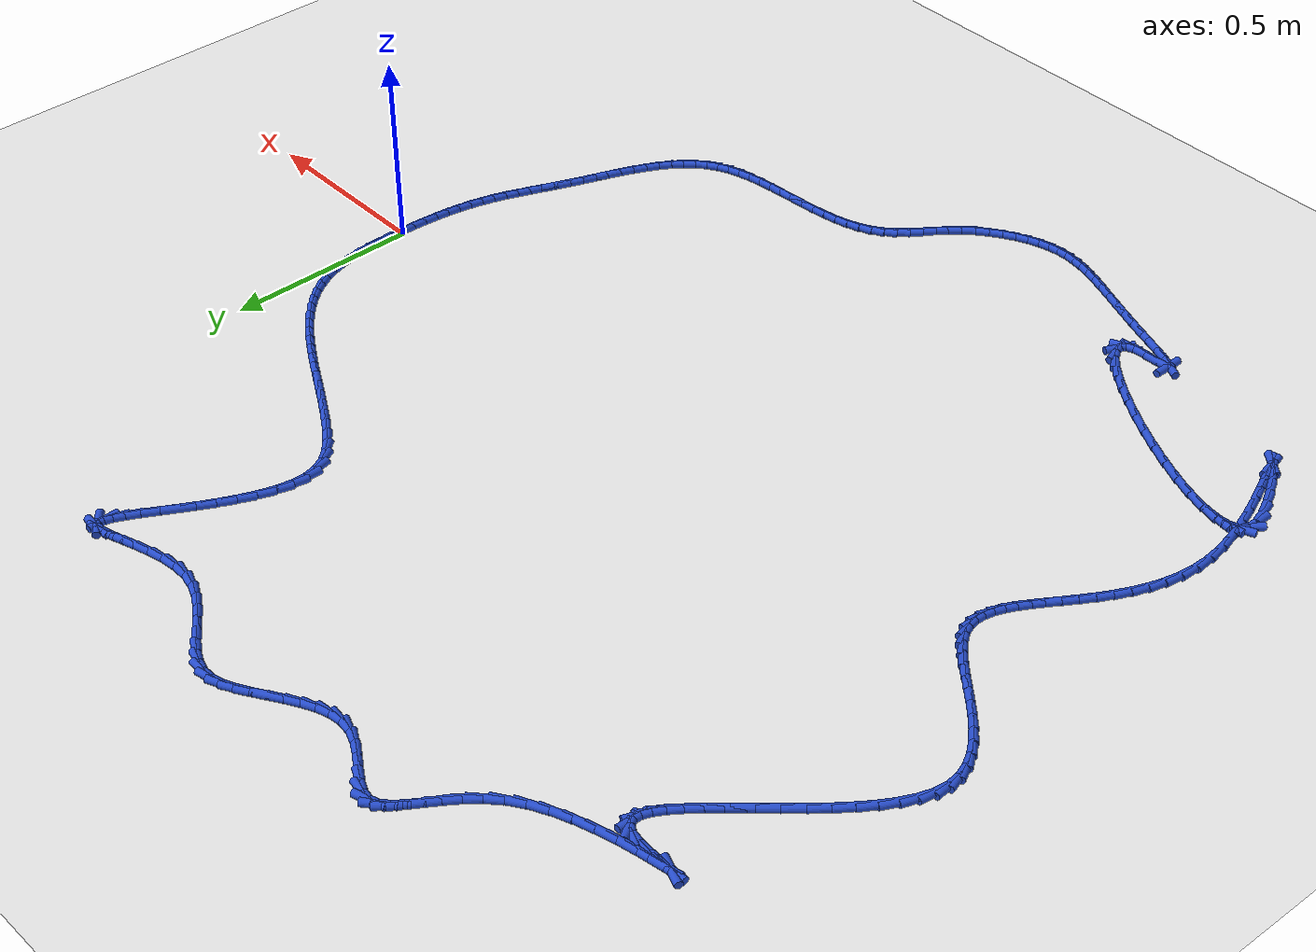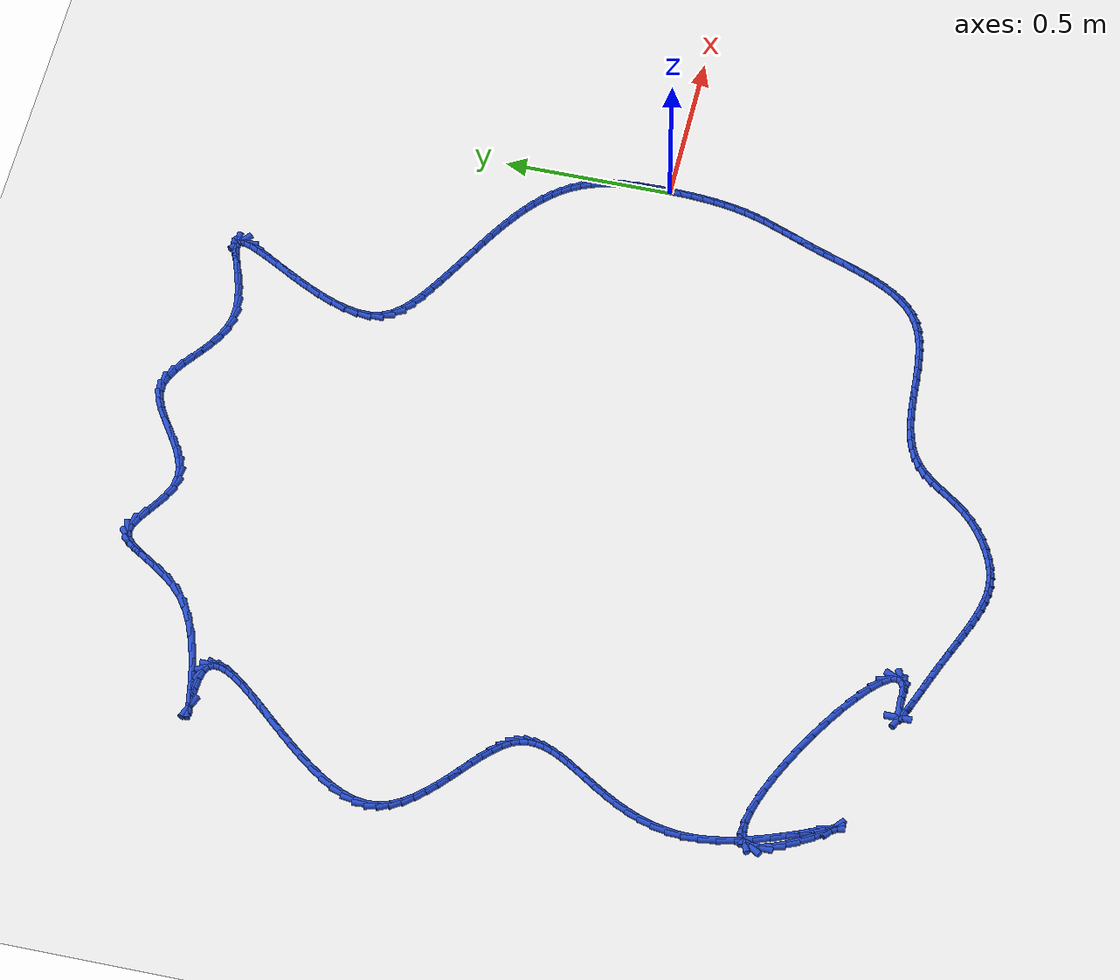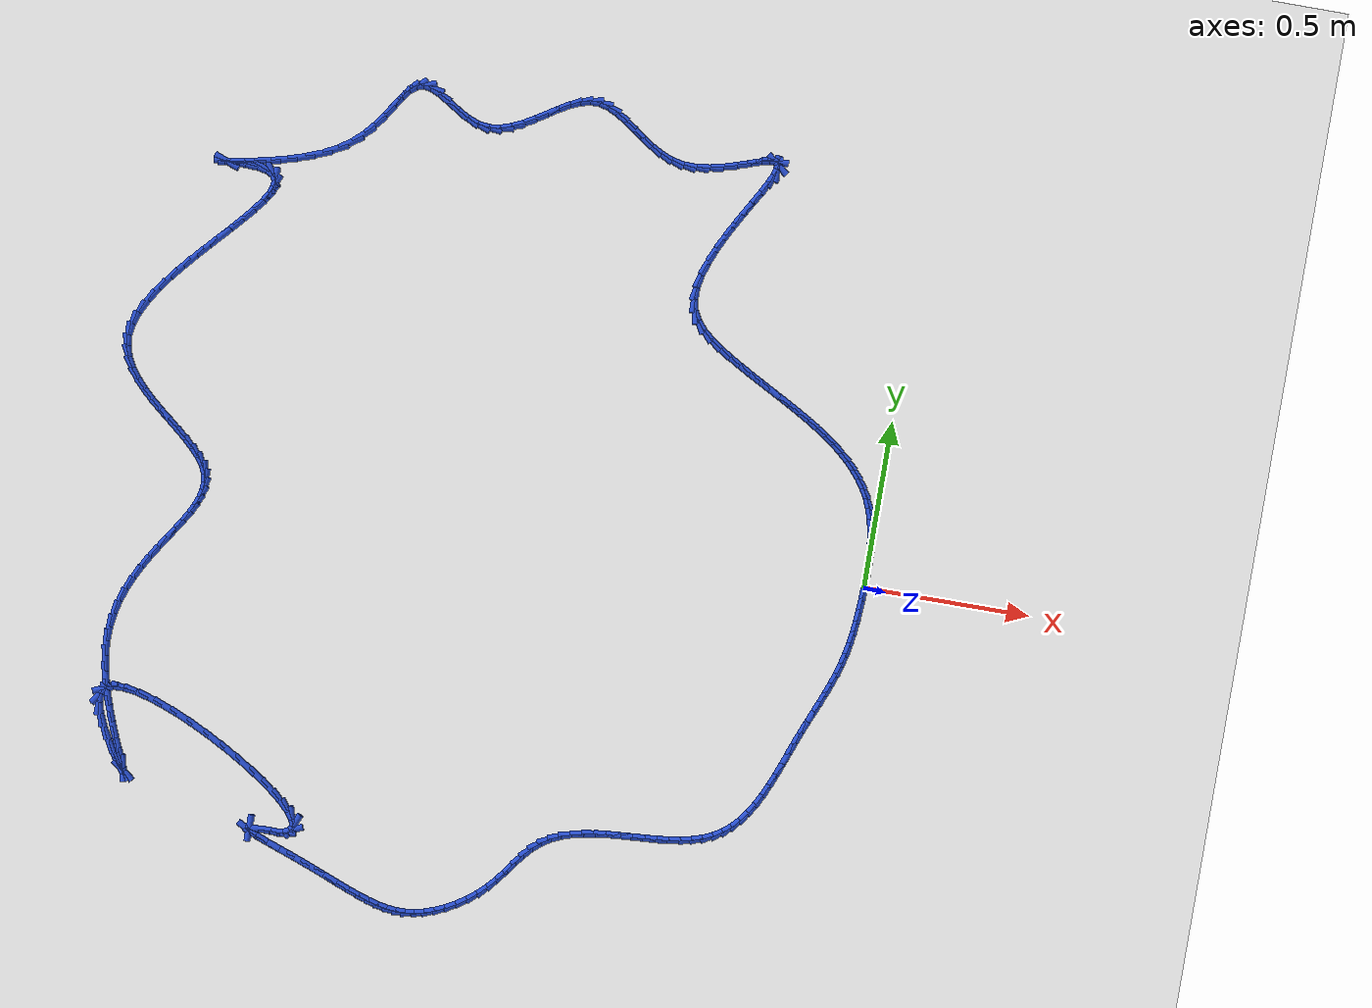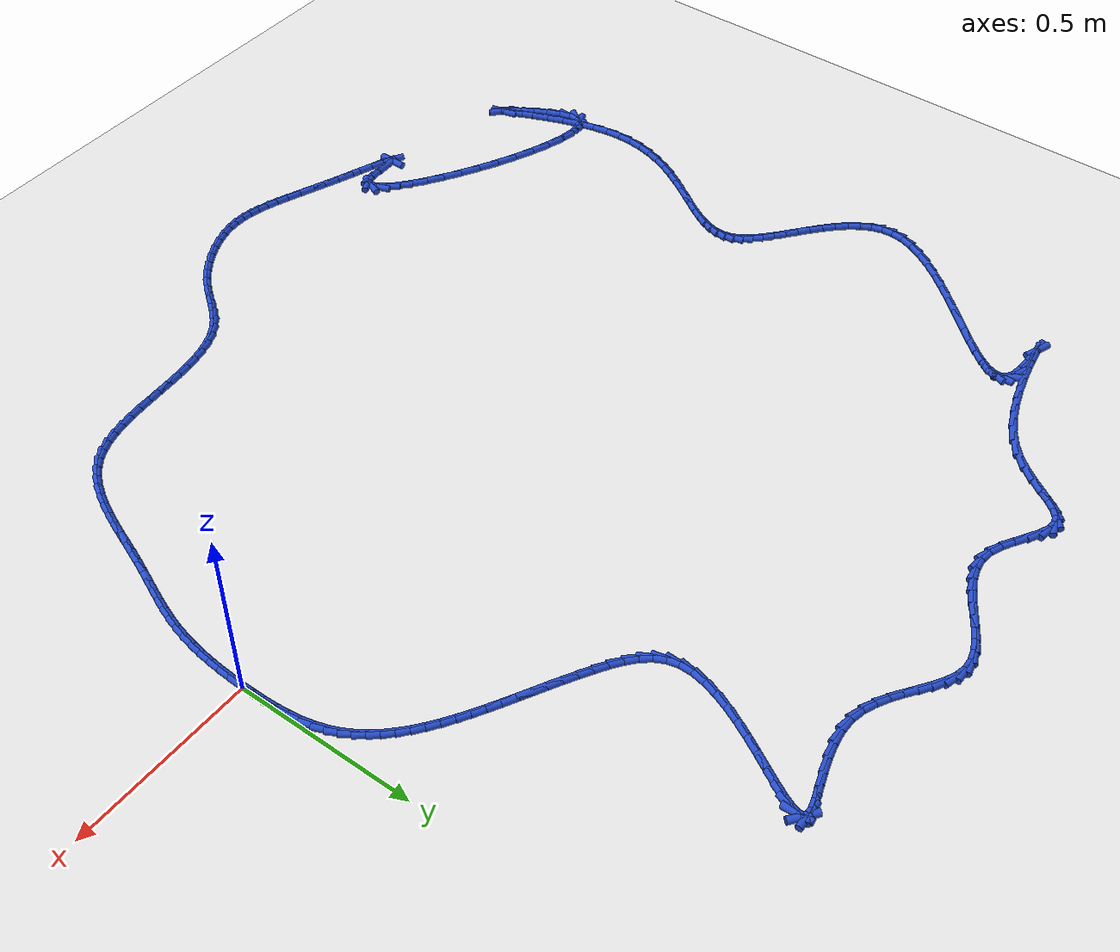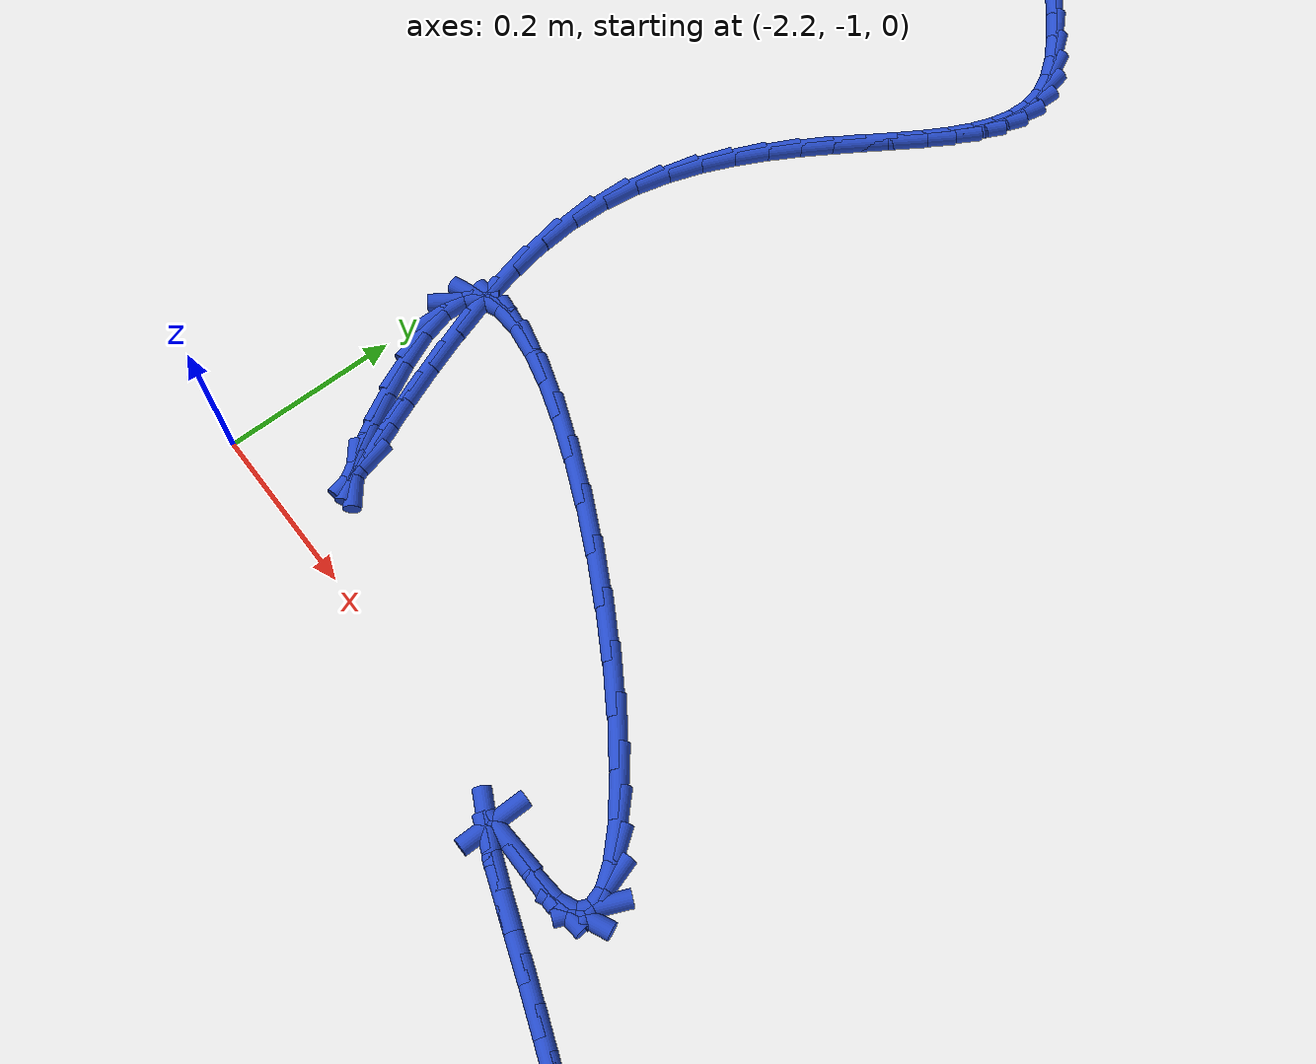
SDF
<sdf version="1.6">
 <world name="default">
  <light name="sun" type="directional">
   <pose>0 0 10 0 -0 0</pose>
   <diffuse>0.8 0.8 0.8 1</diffuse>
   <specular>0.2 0.2 0.2 1</specular>
   <attenuation>
    <range>1000</range>
    <constant>0.9</constant>
    <linear>0.01</linear>
    <quadratic>0.001</quadratic>
   </attenuation>
   <direction>-0.5 0.1 -0.9</direction>
  </light>
  <model name="ground_plane">
   <static>1</static>
   <link name="link">
    <collision name="collision">
     <geometry><plane><normal>0 0 1</normal><size>100 100</size></plane></geometry>
     <surface><friction><ode><mu>100</mu><mu2>50</mu2></ode></friction></surface>
    </collision>
    <visual name="visual">
     <cast_shadows>0</cast_shadows>
     <geometry><plane><normal>0 0 1</normal><size>100 100</size></plane></geometry>
     <material>
      <script><uri>file://media/materials/scripts/gazebo.material</uri><name>Gazebo/WhiteGlow</name></script>
     </material>
    </visual>
   </link>
  </model>
  <gravity>0 0 -9.8</gravity>
  <magnetic_field>6e-06 2.3e-05 -4.2e-05</magnetic_field>
  <atmosphere type="adiabatic"/>
  <physics name="default_physics" default="0" type="ode">
   <max_step_size>0.001</max_step_size>
   <real_time_factor>1</real_time_factor>
   <real_time_update_rate>1000</real_time_update_rate>
  </physics>
  <scene><ambient>0.4 0.4 0.4 1</ambient><background>0.7 0.7 0.7 1</background><shadows>1</shadows></scene>
  <spherical_coordinates>
   <surface_model>EARTH_WGS84</surface_model>
   <latitude_deg>0</latitude_deg>
   <longitude_deg>0</longitude_deg>
   <elevation>0</elevation>
   <heading_deg>0</heading_deg>
  </spherical_coordinates>
  <model name="line">
   <link name="link_0">
    <pose>1.2793585635328952e-17 6.938893903907228e-18 0.01 0 1.57 1.560720310183343</pose>
    <collision name="collision">
     <geometry><cylinder><radius>0.01</radius><length>0.08</length></cylinder></geometry>
    </collision>
    <visual name="visual">
     <material>
      <script><name>Gazebo/Blue</name><uri>file://media/materials/scripts/gazebo.material</uri></script>
     </material>
     <geometry><cylinder><radius>0.01</radius><length>0.08</length></cylinder></geometry>
    </visual>
   </link>
   <link name="link_1">
    <pose>0.0003561060510922249 0.03534075154741206 0.01 0 1.57 -1.5546245115065553</pose>
    <collision name="collision">
     <geometry><cylinder><radius>0.01</radius><length>0.08</length></cylinder></geometry>
    </collision>
    <visual name="visual">
     <material>
      <script><name>Gazebo/Blue</name><uri>file://media/materials/scripts/gazebo.material</uri></script>
     </material>
     <geometry><cylinder><radius>0.01</radius><length>0.08</length></cylinder></geometry>
    </visual>
   </link>
   <link name="link_2">
    <pose>-0.0002157422022764675 0.07069846439136131 0.01 0 1.57 -1.5190362888300548</pose>
    <collision name="collision">
     <geometry><cylinder><radius>0.01</radius><length>0.08</length></cylinder></geometry>
    </collision>
    <visual name="visual">
     <material>
      <script><name>Gazebo/Blue</name><uri>file://media/materials/scripts/gazebo.material</uri></script>
     </material>
     <geometry><cylinder><radius>0.01</radius><length>0.08</length></cylinder></geometry>
    </visual>
   </link>
   <link name="link_3">
    <pose>-0.0020321122549496508 0.10575925171513278 0.01 0 1.57 -1.473069108385165</pose>
    <collision name="collision">
     <geometry><cylinder><radius>0.01</radius><length>0.08</length></cylinder></geometry>
    </collision>
    <visual name="visual">
     <material>
      <script><name>Gazebo/Blue</name><uri>file://media/materials/scripts/gazebo.material</uri></script>
     </material>
     <geometry><cylinder><radius>0.01</radius><length>0.08</length></cylinder></geometry>
    </visual>
   </link>
   <link name="link_4">
    <pose>-0.005409571601770914 0.14020922670201147 0.01 0 1.57 -1.4153106896293728</pose>
    <collision name="collision">
     <geometry><cylinder><radius>0.01</radius><length>0.08</length></cylinder></geometry>
    </collision>
    <visual name="visual">
     <material>
      <script><name>Gazebo/Blue</name><uri>file://media/materials/scripts/gazebo.material</uri></script>
     </material>
     <geometry><cylinder><radius>0.01</radius><length>0.08</length></cylinder></geometry>
    </visual>
   </link>
   <link name="link_5">
    <pose>-0.010664687737583847 0.17373450253528236 0.01 0 1.57 -1.3440396528830696</pose>
    <collision name="collision">
     <geometry><cylinder><radius>0.01</radius><length>0.08</length></cylinder></geometry>
    </collision>
    <visual name="visual">
     <material>
      <script><name>Gazebo/Blue</name><uri>file://media/materials/scripts/gazebo.material</uri></script>
     </material>
     <geometry><cylinder><radius>0.01</radius><length>0.08</length></cylinder></geometry>
    </visual>
   </link>
   <link name="link_6">
    <pose>-0.018114028157232044 0.20602119239823052 0.01 0 1.57 -1.2574030290645206</pose>
    <collision name="collision">
     <geometry><cylinder><radius>0.01</radius><length>0.08</length></cylinder></geometry>
    </collision>
    <visual name="visual">
     <material>
      <script><name>Gazebo/Blue</name><uri>file://media/materials/scripts/gazebo.material</uri></script>
     </material>
     <geometry><cylinder><radius>0.01</radius><length>0.08</length></cylinder></geometry>
    </visual>
   </link>
   <link name="link_7">
    <pose>-0.028074160355559097 0.23675540947414092 0.01 0 1.57 -1.1564193268851086</pose>
    <collision name="collision">
     <geometry><cylinder><radius>0.01</radius><length>0.08</length></cylinder></geometry>
    </collision>
    <visual name="visual">
     <material>
      <script><name>Gazebo/Blue</name><uri>file://media/materials/scripts/gazebo.material</uri></script>
     </material>
     <geometry><cylinder><radius>0.01</radius><length>0.08</length></cylinder></geometry>
    </visual>
   </link>
   <link name="link_8">
    <pose>-0.04079735476901256 0.2656819510736706 0.01 0 1.57 -1.0549637227854383</pose>
    <collision name="collision">
     <geometry><cylinder><radius>0.01</radius><length>0.08</length></cylinder></geometry>
    </collision>
    <visual name="visual">
     <material>
      <script><name>Gazebo/Blue</name><uri>file://media/materials/scripts/gazebo.material</uri></script>
     </material>
     <geometry><cylinder><radius>0.01</radius><length>0.08</length></cylinder></geometry>
    </visual>
   </link>
   <link name="link_9">
    <pose>-0.05620263337087797 0.29284977142766355 0.01 0 1.57 -0.9598250668806347</pose>
    <collision name="collision">
     <geometry><cylinder><radius>0.01</radius><length>0.08</length></cylinder></geometry>
    </collision>
    <visual name="visual">
     <material>
      <script><name>Gazebo/Blue</name><uri>file://media/materials/scripts/gazebo.material</uri></script>
     </material>
     <geometry><cylinder><radius>0.01</radius><length>0.08</length></cylinder></geometry>
    </visual>
   </link>
   <link name="link_10">
    <pose>-0.07410138125429766 0.31840606528592075 0.01 0 1.57 -0.8729581789027131</pose>
    <collision name="collision">
     <geometry><cylinder><radius>0.01</radius><length>0.08</length></cylinder></geometry>
    </collision>
    <visual name="visual">
     <material>
      <script><name>Gazebo/Blue</name><uri>file://media/materials/scripts/gazebo.material</uri></script>
     </material>
     <geometry><cylinder><radius>0.01</radius><length>0.08</length></cylinder></geometry>
    </visual>
   </link>
   <link name="link_11">
    <pose>-0.09430492996516908 0.3424980762709823 0.01 0 1.57 -0.7954941537757592</pose>
    <collision name="collision">
     <geometry><cylinder><radius>0.01</radius><length>0.08</length></cylinder></geometry>
    </collision>
    <visual name="visual">
     <material>
      <script><name>Gazebo/Blue</name><uri>file://media/materials/scripts/gazebo.material</uri></script>
     </material>
     <geometry><cylinder><radius>0.01</radius><length>0.08</length></cylinder></geometry>
    </visual>
   </link>
   <link name="link_12">
    <pose>-0.1166246110493896 0.36527304800538823 0.01 0 1.57 -0.7278427136286466</pose>
    <collision name="collision">
     <geometry><cylinder><radius>0.01</radius><length>0.08</length></cylinder></geometry>
    </collision>
    <visual name="visual">
     <material>
      <script><name>Gazebo/Blue</name><uri>file://media/materials/scripts/gazebo.material</uri></script>
     </material>
     <geometry><cylinder><radius>0.01</radius><length>0.08</length></cylinder></geometry>
    </visual>
   </link>
   <link name="link_13">
    <pose>-0.14087175605285673 0.38687822411167855 0.01 0 1.57 -0.66988542396125</pose>
    <collision name="collision">
     <geometry><cylinder><radius>0.01</radius><length>0.08</length></cylinder></geometry>
    </collision>
    <visual name="visual">
     <material>
      <script><name>Gazebo/Blue</name><uri>file://media/materials/scripts/gazebo.material</uri></script>
     </material>
     <geometry><cylinder><radius>0.01</radius><length>0.08</length></cylinder></geometry>
    </visual>
   </link>
   <link name="link_14">
    <pose>-0.16685769652146776 0.4074608482123933 0.01 0 1.57 -0.6211793957976091</pose>
    <collision name="collision">
     <geometry><cylinder><radius>0.01</radius><length>0.08</length></cylinder></geometry>
    </collision>
    <visual name="visual">
     <material>
      <script><name>Gazebo/Blue</name><uri>file://media/materials/scripts/gazebo.material</uri></script>
     </material>
     <geometry><cylinder><radius>0.01</radius><length>0.08</length></cylinder></geometry>
    </visual>
   </link>
   <link name="link_15">
    <pose>-0.19439376400112018 0.4271681639300725 0.01 0 1.57 -0.5811251205386989</pose>
    <collision name="collision">
     <geometry><cylinder><radius>0.01</radius><length>0.08</length></cylinder></geometry>
    </collision>
    <visual name="visual">
     <material>
      <script><name>Gazebo/Blue</name><uri>file://media/materials/scripts/gazebo.material</uri></script>
     </material>
     <geometry><cylinder><radius>0.01</radius><length>0.08</length></cylinder></geometry>
    </visual>
   </link>
   <link name="link_16">
    <pose>-0.22329129003771145 0.4461474148872562 0.01 0 1.57 -0.5490849501158122</pose>
    <collision name="collision">
     <geometry><cylinder><radius>0.01</radius><length>0.08</length></cylinder></geometry>
    </collision>
    <visual name="visual">
     <material>
      <script><name>Gazebo/Blue</name><uri>file://media/materials/scripts/gazebo.material</uri></script>
     </material>
     <geometry><cylinder><radius>0.01</radius><length>0.08</length></cylinder></geometry>
    </visual>
   </link>
   <link name="link_17">
    <pose>-0.253361606177139 0.46454584470648447 0.01 0 1.57 -0.5244572676597984</pose>
    <collision name="collision">
     <geometry><cylinder><radius>0.01</radius><length>0.08</length></cylinder></geometry>
    </collision>
    <visual name="visual">
     <material>
      <script><name>Gazebo/Blue</name><uri>file://media/materials/scripts/gazebo.material</uri></script>
     </material>
     <geometry><cylinder><radius>0.01</radius><length>0.08</length></cylinder></geometry>
    </visual>
   </link>
   <link name="link_18">
    <pose>-0.28441604396530007 0.48251069701029725 0.01 0 1.57 -0.5067177754159372</pose>
    <collision name="collision">
     <geometry><cylinder><radius>0.01</radius><length>0.08</length></cylinder></geometry>
    </collision>
    <visual name="visual">
     <material>
      <script><name>Gazebo/Blue</name><uri>file://media/materials/scripts/gazebo.material</uri></script>
     </material>
     <geometry><cylinder><radius>0.01</radius><length>0.08</length></cylinder></geometry>
    </visual>
   </link>
   <link name="link_19">
    <pose>-0.31626593494809224 0.5001892154212346 0.01 0 1.57 -0.49543910347332776</pose>
    <collision name="collision">
     <geometry><cylinder><radius>0.01</radius><length>0.08</length></cylinder></geometry>
    </collision>
    <visual name="visual">
     <material>
      <script><name>Gazebo/Blue</name><uri>file://media/materials/scripts/gazebo.material</uri></script>
     </material>
     <geometry><cylinder><radius>0.01</radius><length>0.08</length></cylinder></geometry>
    </visual>
   </link>
   <link name="link_20">
    <pose>-0.3487226106714128 0.5177286435618366 0.01 0 1.57 -0.4902973190634133</pose>
    <collision name="collision">
     <geometry><cylinder><radius>0.01</radius><length>0.08</length></cylinder></geometry>
    </collision>
    <visual name="visual">
     <material>
      <script><name>Gazebo/Blue</name><uri>file://media/materials/scripts/gazebo.material</uri></script>
     </material>
     <geometry><cylinder><radius>0.01</radius><length>0.08</length></cylinder></geometry>
    </visual>
   </link>
   <link name="link_21">
    <pose>-0.38159740268115927 0.5352762250546431 0.01 0 1.57 -0.491071039803365</pose>
    <collision name="collision">
     <geometry><cylinder><radius>0.01</radius><length>0.08</length></cylinder></geometry>
    </collision>
    <visual name="visual">
     <material>
      <script><name>Gazebo/Blue</name><uri>file://media/materials/scripts/gazebo.material</uri></script>
     </material>
     <geometry><cylinder><radius>0.01</radius><length>0.08</length></cylinder></geometry>
    </visual>
   </link>
   <link name="link_22">
    <pose>-0.41470164252322916 0.5529792035221943 0.01 0 1.57 -0.4976364902991608</pose>
    <collision name="collision">
     <geometry><cylinder><radius>0.01</radius><length>0.08</length></cylinder></geometry>
    </collision>
    <visual name="visual">
     <material>
      <script><name>Gazebo/Blue</name><uri>file://media/materials/scripts/gazebo.material</uri></script>
     </material>
     <geometry><cylinder><radius>0.01</radius><length>0.08</length></cylinder></geometry>
    </visual>
   </link>
   <link name="link_23">
    <pose>-0.4478466617435196 0.5709848225870303 0.01 0 1.57 -0.509960086845654</pose>
    <collision name="collision">
     <geometry><cylinder><radius>0.01</radius><length>0.08</length></cylinder></geometry>
    </collision>
    <visual name="visual">
     <material>
      <script><name>Gazebo/Blue</name><uri>file://media/materials/scripts/gazebo.material</uri></script>
     </material>
     <geometry><cylinder><radius>0.01</radius><length>0.08</length></cylinder></geometry>
    </visual>
   </link>
   <link name="link_24">
    <pose>-0.48084379188792825 0.589440325871691 0.01 0 1.57 -0.528088850275168</pose>
    <collision name="collision">
     <geometry><cylinder><radius>0.01</radius><length>0.08</length></cylinder></geometry>
    </collision>
    <visual name="visual">
     <material>
      <script><name>Gazebo/Blue</name><uri>file://media/materials/scripts/gazebo.material</uri></script>
     </material>
     <geometry><cylinder><radius>0.01</radius><length>0.08</length></cylinder></geometry>
    </visual>
   </link>
   <link name="link_25">
    <pose>-0.5135043645023525 0.6084929569987165 0.01 0 1.57 -0.5555644324495408</pose>
    <collision name="collision">
     <geometry><cylinder><radius>0.01</radius><length>0.08</length></cylinder></geometry>
    </collision>
    <visual name="visual">
     <material>
      <script><name>Gazebo/Blue</name><uri>file://media/materials/scripts/gazebo.material</uri></script>
     </material>
     <geometry><cylinder><radius>0.01</radius><length>0.08</length></cylinder></geometry>
    </visual>
   </link>
   <link name="link_26">
    <pose>-0.545481683929184 0.6283440801608842 0.01 0 1.57 -0.6128239445450531</pose>
    <collision name="collision">
     <geometry><cylinder><radius>0.01</radius><length>0.08</length></cylinder></geometry>
    </collision>
    <visual name="visual">
     <material>
      <script><name>Gazebo/Blue</name><uri>file://media/materials/scripts/gazebo.material</uri></script>
     </material>
     <geometry><cylinder><radius>0.01</radius><length>0.08</length></cylinder></geometry>
    </visual>
   </link>
   <link name="link_27">
    <pose>-0.5755596420754402 0.6494928126955598 0.01 0 1.57 -0.7127521897390728</pose>
    <collision name="collision">
     <geometry><cylinder><radius>0.01</radius><length>0.08</length></cylinder></geometry>
    </collision>
    <visual name="visual">
     <material>
      <script><name>Gazebo/Blue</name><uri>file://media/materials/scripts/gazebo.material</uri></script>
     </material>
     <geometry><cylinder><radius>0.01</radius><length>0.08</length></cylinder></geometry>
    </visual>
   </link>
   <link name="link_28">
    <pose>-0.6022247270509058 0.6725401256889569 0.01 0 1.57 -0.8657677997520344</pose>
    <collision name="collision">
     <geometry><cylinder><radius>0.01</radius><length>0.08</length></cylinder></geometry>
    </collision>
    <visual name="visual">
     <material>
      <script><name>Gazebo/Blue</name><uri>file://media/materials/scripts/gazebo.material</uri></script>
     </material>
     <geometry><cylinder><radius>0.01</radius><length>0.08</length></cylinder></geometry>
    </visual>
   </link>
   <link name="link_29">
    <pose>-0.6239631670880293 0.6980870792291144 0.01 0 1.57 -1.0803153326070458</pose>
    <collision name="collision">
     <geometry><cylinder><radius>0.01</radius><length>0.08</length></cylinder></geometry>
    </collision>
    <visual name="visual">
     <material>
      <script><name>Gazebo/Blue</name><uri>file://media/materials/scripts/gazebo.material</uri></script>
     </material>
     <geometry><cylinder><radius>0.01</radius><length>0.08</length></cylinder></geometry>
    </visual>
   </link>
   <link name="link_30">
    <pose>-0.6392611904192603 0.7267347334040714 0.01 0 1.57 -1.3448013934974803</pose>
    <collision name="collision">
     <geometry><cylinder><radius>0.01</radius><length>0.08</length></cylinder></geometry>
    </collision>
    <visual name="visual">
     <material>
      <script><name>Gazebo/Blue</name><uri>file://media/materials/scripts/gazebo.material</uri></script>
     </material>
     <geometry><cylinder><radius>0.01</radius><length>0.08</length></cylinder></geometry>
    </visual>
   </link>
   <link name="link_31">
    <pose>-0.6466890578904758 0.7590406724687265 0.01 0 1.57 1.5584059713228573</pose>
    <collision name="collision">
     <geometry><cylinder><radius>0.01</radius><length>0.08</length></cylinder></geometry>
    </collision>
    <visual name="visual">
     <material>
      <script><name>Gazebo/Blue</name><uri>file://media/materials/scripts/gazebo.material</uri></script>
     </material>
     <geometry><cylinder><radius>0.01</radius><length>0.08</length></cylinder></geometry>
    </visual>
   </link>
   <link name="link_32">
    <pose>-0.6462456751714738 0.7948233447467188 0.01 0 1.57 1.3877105082147523</pose>
    <collision name="collision">
     <geometry><cylinder><radius>0.01</radius><length>0.08</length></cylinder></geometry>
    </collision>
    <visual name="visual">
     <material>
      <script><name>Gazebo/Blue</name><uri>file://media/materials/scripts/gazebo.material</uri></script>
     </material>
     <geometry><cylinder><radius>0.01</radius><length>0.08</length></cylinder></geometry>
    </visual>
   </link>
   <link name="link_33">
    <pose>-0.6391244765768106 0.8332831869835289 0.01 0 1.57 1.2686046594420235</pose>
    <collision name="collision">
     <geometry><cylinder><radius>0.01</radius><length>0.08</length></cylinder></geometry>
    </collision>
    <visual name="visual">
     <material>
      <script><name>Gazebo/Blue</name><uri>file://media/materials/scripts/gazebo.material</uri></script>
     </material>
     <geometry><cylinder><radius>0.01</radius><length>0.08</length></cylinder></geometry>
    </visual>
   </link>
   <link name="link_34">
    <pose>-0.6265556351311244 0.873601628470697 0.01 0 1.57 1.185236775959328</pose>
    <collision name="collision">
     <geometry><cylinder><radius>0.01</radius><length>0.08</length></cylinder></geometry>
    </collision>
    <visual name="visual">
     <material>
      <script><name>Gazebo/Blue</name><uri>file://media/materials/scripts/gazebo.material</uri></script>
     </material>
     <geometry><cylinder><radius>0.01</radius><length>0.08</length></cylinder></geometry>
    </visual>
   </link>
   <link name="link_35">
    <pose>-0.609769323859054 0.9149600984997613 0.01 0 1.57 1.1268939732735868</pose>
    <collision name="collision">
     <geometry><cylinder><radius>0.01</radius><length>0.08</length></cylinder></geometry>
    </collision>
    <visual name="visual">
     <material>
      <script><name>Gazebo/Blue</name><uri>file://media/materials/scripts/gazebo.material</uri></script>
     </material>
     <geometry><cylinder><radius>0.01</radius><length>0.08</length></cylinder></geometry>
    </visual>
   </link>
   <link name="link_36">
    <pose>-0.5899957157852381 0.9565400263622604 0.01 0 1.57 1.0870671492082775</pose>
    <collision name="collision">
     <geometry><cylinder><radius>0.01</radius><length>0.08</length></cylinder></geometry>
    </collision>
    <visual name="visual">
     <material>
      <script><name>Gazebo/Blue</name><uri>file://media/materials/scripts/gazebo.material</uri></script>
     </material>
     <geometry><cylinder><radius>0.01</radius><length>0.08</length></cylinder></geometry>
    </visual>
   </link>
   <link name="link_37">
    <pose>-0.5684649839343152 0.9975228413497345 0.01 0 1.57 1.0622323490488503</pose>
    <collision name="collision">
     <geometry><cylinder><radius>0.01</radius><length>0.08</length></cylinder></geometry>
    </collision>
    <visual name="visual">
     <material>
      <script><name>Gazebo/Blue</name><uri>file://media/materials/scripts/gazebo.material</uri></script>
     </material>
     <geometry><cylinder><radius>0.01</radius><length>0.08</length></cylinder></geometry>
    </visual>
   </link>
   <link name="link_38">
    <pose>-0.5464073013309236 1.0370899727537224 0.01 0 1.57 1.0512184469167245</pose>
    <collision name="collision">
     <geometry><cylinder><radius>0.01</radius><length>0.08</length></cylinder></geometry>
    </collision>
    <visual name="visual">
     <material>
      <script><name>Gazebo/Blue</name><uri>file://media/materials/scripts/gazebo.material</uri></script>
     </material>
     <geometry><cylinder><radius>0.01</radius><length>0.08</length></cylinder></geometry>
    </visual>
   </link>
   <link name="link_39">
    <pose>-0.5250528409997021 1.0744228498657626 0.01 0 1.57 1.055342224895024</pose>
    <collision name="collision">
     <geometry><cylinder><radius>0.01</radius><length>0.08</length></cylinder></geometry>
    </collision>
    <visual name="visual">
     <material>
      <script><name>Gazebo/Blue</name><uri>file://media/materials/scripts/gazebo.material</uri></script>
     </material>
     <geometry><cylinder><radius>0.01</radius><length>0.08</length></cylinder></geometry>
    </visual>
   </link>
   <link name="link_40">
    <pose>-0.5056317759652891 1.1087029019773942 0.01 0 1.57 1.079827042895526</pose>
    <collision name="collision">
     <geometry><cylinder><radius>0.01</radius><length>0.08</length></cylinder></geometry>
    </collision>
    <visual name="visual">
     <material>
      <script><name>Gazebo/Blue</name><uri>file://media/materials/scripts/gazebo.material</uri></script>
     </material>
     <geometry><cylinder><radius>0.01</radius><length>0.08</length></cylinder></geometry>
    </visual>
   </link>
   <link name="link_41">
    <pose>-0.4893742792523235 1.1391115583801572 0.01 0 1.57 1.138594013375491</pose>
    <collision name="collision">
     <geometry><cylinder><radius>0.01</radius><length>0.08</length></cylinder></geometry>
    </collision>
    <visual name="visual">
     <material>
      <script><name>Gazebo/Blue</name><uri>file://media/materials/scripts/gazebo.material</uri></script>
     </material>
     <geometry><cylinder><radius>0.01</radius><length>0.08</length></cylinder></geometry>
    </visual>
   </link>
   <link name="link_42">
    <pose>-0.4775105238854435 1.1648302483655897 0.01 0 1.57 1.2713334405244971</pose>
    <collision name="collision">
     <geometry><cylinder><radius>0.01</radius><length>0.08</length></cylinder></geometry>
    </collision>
    <visual name="visual">
     <material>
      <script><name>Gazebo/Blue</name><uri>file://media/materials/scripts/gazebo.material</uri></script>
     </material>
     <geometry><cylinder><radius>0.01</radius><length>0.08</length></cylinder></geometry>
    </visual>
   </link>
   <link name="link_43">
    <pose>-0.47127068288928786 1.1850404012252314 0.01 0 1.57 -1.5265808063890085</pose>
    <collision name="collision">
     <geometry><cylinder><radius>0.01</radius><length>0.08</length></cylinder></geometry>
    </collision>
    <visual name="visual">
     <material>
      <script><name>Gazebo/Blue</name><uri>file://media/materials/scripts/gazebo.material</uri></script>
     </material>
     <geometry><cylinder><radius>0.01</radius><length>0.08</length></cylinder></geometry>
    </visual>
   </link>
   <link name="link_44">
    <pose>-0.4718849292884951 1.1989234462506209 0.01 0 1.57 -0.6590452512910231</pose>
    <collision name="collision">
     <geometry><cylinder><radius>0.01</radius><length>0.08</length></cylinder></geometry>
    </collision>
    <visual name="visual">
     <material>
      <script><name>Gazebo/Blue</name><uri>file://media/materials/scripts/gazebo.material</uri></script>
     </material>
     <geometry><cylinder><radius>0.01</radius><length>0.08</length></cylinder></geometry>
    </visual>
   </link>
   <link name="link_45">
    <pose>-0.4805832748494404 1.2056609778249119 0.01 0 1.57 0.03743367609186603</pose>
    <collision name="collision">
     <geometry><cylinder><radius>0.01</radius><length>0.08</length></cylinder></geometry>
    </collision>
    <visual name="visual">
     <material>
      <script><name>Gazebo/Blue</name><uri>file://media/materials/scripts/gazebo.material</uri></script>
     </material>
     <geometry><cylinder><radius>0.01</radius><length>0.08</length></cylinder></geometry>
    </visual>
   </link>
   <link name="link_46">
    <pose>-0.4980362782983033 1.2050073424096837 0.01 0 1.57 0.2513064341759677</pose>
    <collision name="collision">
     <geometry><cylinder><radius>0.01</radius><length>0.08</length></cylinder></geometry>
    </collision>
    <visual name="visual">
     <material>
      <script><name>Gazebo/Blue</name><uri>file://media/materials/scripts/gazebo.material</uri></script>
     </material>
     <geometry><cylinder><radius>0.01</radius><length>0.08</length></cylinder></geometry>
    </visual>
   </link>
   <link name="link_47">
    <pose>-0.5231024578715252 1.198572001877682 0.01 0 1.57 0.31718513528585807</pose>
    <collision name="collision">
     <geometry><cylinder><radius>0.01</radius><length>0.08</length></cylinder></geometry>
    </collision>
    <visual name="visual">
     <material>
      <script><name>Gazebo/Blue</name><uri>file://media/materials/scripts/gazebo.material</uri></script>
     </material>
     <geometry><cylinder><radius>0.01</radius><length>0.08</length></cylinder></geometry>
    </visual>
   </link>
   <link name="link_48">
    <pose>-0.5542741236470079 1.1883393315776178 0.01 0 1.57 0.3248288836402233</pose>
    <collision name="collision">
     <geometry><cylinder><radius>0.01</radius><length>0.08</length></cylinder></geometry>
    </collision>
    <visual name="visual">
     <material>
      <script><name>Gazebo/Blue</name><uri>file://media/materials/scripts/gazebo.material</uri></script>
     </material>
     <geometry><cylinder><radius>0.01</radius><length>0.08</length></cylinder></geometry>
    </visual>
   </link>
   <link name="link_49">
    <pose>-0.5900435857026539 1.1762937068582036 0.01 0 1.57 0.29655632443599317</pose>
    <collision name="collision">
     <geometry><cylinder><radius>0.01</radius><length>0.08</length></cylinder></geometry>
    </collision>
    <visual name="visual">
     <material>
      <script><name>Gazebo/Blue</name><uri>file://media/materials/scripts/gazebo.material</uri></script>
     </material>
     <geometry><cylinder><radius>0.01</radius><length>0.08</length></cylinder></geometry>
    </visual>
   </link>
   <link name="link_50">
    <pose>-0.6289031541163659 1.1644195030681506 0.01 0 1.57 0.23583326406208197</pose>
    <collision name="collision">
     <geometry><cylinder><radius>0.01</radius><length>0.08</length></cylinder></geometry>
    </collision>
    <visual name="visual">
     <material>
      <script><name>Gazebo/Blue</name><uri>file://media/materials/scripts/gazebo.material</uri></script>
     </material>
     <geometry><cylinder><radius>0.01</radius><length>0.08</length></cylinder></geometry>
    </visual>
   </link>
   <link name="link_51">
    <pose>-0.6693451389660456 1.1547010955561705 0.01 0 1.57 0.136817276472193</pose>
    <collision name="collision">
     <geometry><cylinder><radius>0.01</radius><length>0.08</length></cylinder></geometry>
    </collision>
    <visual name="visual">
     <material>
      <script><name>Gazebo/Blue</name><uri>file://media/materials/scripts/gazebo.material</uri></script>
     </material>
     <geometry><cylinder><radius>0.01</radius><length>0.08</length></cylinder></geometry>
    </visual>
   </link>
   <link name="link_52">
    <pose>-0.7098618503295954 1.149122859670975 0.01 0 1.57 -0.013909241696917369</pose>
    <collision name="collision">
     <geometry><cylinder><radius>0.01</radius><length>0.08</length></cylinder></geometry>
    </collision>
    <visual name="visual">
     <material>
      <script><name>Gazebo/Blue</name><uri>file://media/materials/scripts/gazebo.material</uri></script>
     </material>
     <geometry><cylinder><radius>0.01</radius><length>0.08</length></cylinder></geometry>
    </visual>
   </link>
   <link name="link_53">
    <pose>-0.7489469349420264 1.1496665386213587 0.01 0 1.57 -0.20713527541361673</pose>
    <collision name="collision">
     <geometry><cylinder><radius>0.01</radius><length>0.08</length></cylinder></geometry>
    </collision>
    <visual name="visual">
     <material>
      <script><name>Gazebo/Blue</name><uri>file://media/materials/scripts/gazebo.material</uri></script>
     </material>
     <geometry><cylinder><radius>0.01</radius><length>0.08</length></cylinder></geometry>
    </visual>
   </link>
   <link name="link_54">
    <pose>-0.785576314988455 1.1573641806980128 0.01 0 1.57 -0.3752574113976</pose>
    <collision name="collision">
     <geometry><cylinder><radius>0.01</radius><length>0.08</length></cylinder></geometry>
    </collision>
    <visual name="visual">
     <material>
      <script><name>Gazebo/Blue</name><uri>file://media/materials/scripts/gazebo.material</uri></script>
     </material>
     <geometry><cylinder><radius>0.01</radius><length>0.08</length></cylinder></geometry>
    </visual>
   </link>
   <link name="link_55">
    <pose>-0.8199214654390802 1.1708935563529599 0.01 0 1.57 -0.4993399005876167</pose>
    <collision name="collision">
     <geometry><cylinder><radius>0.01</radius><length>0.08</length></cylinder></geometry>
    </collision>
    <visual name="visual">
     <material>
      <script><name>Gazebo/Blue</name><uri>file://media/materials/scripts/gazebo.material</uri></script>
     </material>
     <geometry><cylinder><radius>0.01</radius><length>0.08</length></cylinder></geometry>
    </visual>
   </link>
   <link name="link_56">
    <pose>-0.8523359381512009 1.1885738909488006 0.01 0 1.57 -0.5787934021531784</pose>
    <collision name="collision">
     <geometry><cylinder><radius>0.01</radius><length>0.08</length></cylinder></geometry>
    </collision>
    <visual name="visual">
     <material>
      <script><name>Gazebo/Blue</name><uri>file://media/materials/scripts/gazebo.material</uri></script>
     </material>
     <geometry><cylinder><radius>0.01</radius><length>0.08</length></cylinder></geometry>
    </visual>
   </link>
   <link name="link_57">
    <pose>-0.883173284982117 1.208724409848137 0.01 0 1.57 -0.6154758590339563</pose>
    <collision name="collision">
     <geometry><cylinder><radius>0.01</radius><length>0.08</length></cylinder></geometry>
    </collision>
    <visual name="visual">
     <material>
      <script><name>Gazebo/Blue</name><uri>file://media/materials/scripts/gazebo.material</uri></script>
     </material>
     <geometry><cylinder><radius>0.01</radius><length>0.08</length></cylinder></geometry>
    </visual>
   </link>
   <link name="link_58">
    <pose>-0.9127870577891284 1.22966433841357 0.01 0 1.57 -0.6090414018737079</pose>
    <collision name="collision">
     <geometry><cylinder><radius>0.01</radius><length>0.08</length></cylinder></geometry>
    </collision>
    <visual name="visual">
     <material>
      <script><name>Gazebo/Blue</name><uri>file://media/materials/scripts/gazebo.material</uri></script>
     </material>
     <geometry><cylinder><radius>0.01</radius><length>0.08</length></cylinder></geometry>
    </visual>
   </link>
   <link name="link_59">
    <pose>-0.9415308084295343 1.2497129020077016 0.01 0 1.57 -0.5543687906518694</pose>
    <collision name="collision">
     <geometry><cylinder><radius>0.01</radius><length>0.08</length></cylinder></geometry>
    </collision>
    <visual name="visual">
     <material>
      <script><name>Gazebo/Blue</name><uri>file://media/materials/scripts/gazebo.material</uri></script>
     </material>
     <geometry><cylinder><radius>0.01</radius><length>0.08</length></cylinder></geometry>
    </visual>
   </link>
   <link name="link_60">
    <pose>-0.9697580887606341 1.2671893259931326 0.01 0 1.57 -0.44033113864854867</pose>
    <collision name="collision">
     <geometry><cylinder><radius>0.01</radius><length>0.08</length></cylinder></geometry>
    </collision>
    <visual name="visual">
     <material>
      <script><name>Gazebo/Blue</name><uri>file://media/materials/scripts/gazebo.material</uri></script>
     </material>
     <geometry><cylinder><radius>0.01</radius><length>0.08</length></cylinder></geometry>
    </visual>
   </link>
   <link name="link_61">
    <pose>-0.9978224506397275 1.2804128357324647 0.01 0 1.57 -0.25249485129466703</pose>
    <collision name="collision">
     <geometry><cylinder><radius>0.01</radius><length>0.08</length></cylinder></geometry>
    </collision>
    <visual name="visual">
     <material>
      <script><name>Gazebo/Blue</name><uri>file://media/materials/scripts/gazebo.material</uri></script>
     </material>
     <geometry><cylinder><radius>0.01</radius><length>0.08</length></cylinder></geometry>
    </visual>
   </link>
   <link name="link_62">
    <pose>-1.0260774459241144 1.2877026565882996 0.01 0 1.57 0.008734874273873747</pose>
    <collision name="collision">
     <geometry><cylinder><radius>0.01</radius><length>0.08</length></cylinder></geometry>
    </collision>
    <visual name="visual">
     <material>
      <script><name>Gazebo/Blue</name><uri>file://media/materials/scripts/gazebo.material</uri></script>
     </material>
     <geometry><cylinder><radius>0.01</radius><length>0.08</length></cylinder></geometry>
    </visual>
   </link>
   <link name="link_63">
    <pose>-1.0548682119819996 1.2874511664704362 0.01 0 1.57 0.2566535131797015</pose>
    <collision name="collision">
     <geometry><cylinder><radius>0.01</radius><length>0.08</length></cylinder></geometry>
    </collision>
    <visual name="visual">
     <material>
      <script><name>Gazebo/Blue</name><uri>file://media/materials/scripts/gazebo.material</uri></script>
     </material>
     <geometry><cylinder><radius>0.01</radius><length>0.08</length></cylinder></geometry>
    </visual>
   </link>
   <link name="link_64">
    <pose>-1.084348531764848 1.2797143098873314 0.01 0 1.57 0.4215586029194371</pose>
    <collision name="collision">
     <geometry><cylinder><radius>0.01</radius><length>0.08</length></cylinder></geometry>
    </collision>
    <visual name="visual">
     <material>
      <script><name>Gazebo/Blue</name><uri>file://media/materials/scripts/gazebo.material</uri></script>
     </material>
     <geometry><cylinder><radius>0.01</radius><length>0.08</length></cylinder></geometry>
    </visual>
   </link>
   <link name="link_65">
    <pose>-1.1144820364992036 1.2662011421752153 0.01 0 1.57 0.517733047162859</pose>
    <collision name="collision">
     <geometry><cylinder><radius>0.01</radius><length>0.08</length></cylinder></geometry>
    </collision>
    <visual name="visual">
     <material>
      <script><name>Gazebo/Blue</name><uri>file://media/materials/scripts/gazebo.material</uri></script>
     </material>
     <geometry><cylinder><radius>0.01</radius><length>0.08</length></cylinder></geometry>
    </visual>
   </link>
   <link name="link_66">
    <pose>-1.1452241834638777 1.2486917800372783 0.01 0 1.57 0.5622440133853116</pose>
    <collision name="collision">
     <geometry><cylinder><radius>0.01</radius><length>0.08</length></cylinder></geometry>
    </collision>
    <visual name="visual">
     <material>
      <script><name>Gazebo/Blue</name><uri>file://media/materials/scripts/gazebo.material</uri></script>
     </material>
     <geometry><cylinder><radius>0.01</radius><length>0.08</length></cylinder></geometry>
    </visual>
   </link>
   <link name="link_67">
    <pose>-1.1765304299376818 1.228966340176711 0.01 0 1.57 0.5646828335004401</pose>
    <collision name="collision">
     <geometry><cylinder><radius>0.01</radius><length>0.08</length></cylinder></geometry>
    </collision>
    <visual name="visual">
     <material>
      <script><name>Gazebo/Blue</name><uri>file://media/materials/scripts/gazebo.material</uri></script>
     </material>
     <geometry><cylinder><radius>0.01</radius><length>0.08</length></cylinder></geometry>
    </visual>
   </link>
   <link name="link_68">
    <pose>-1.2083562331994264 1.2088049392967057 0.01 0 1.57 0.5274991329047906</pose>
    <collision name="collision">
     <geometry><cylinder><radius>0.01</radius><length>0.08</length></cylinder></geometry>
    </collision>
    <visual name="visual">
     <material>
      <script><name>Gazebo/Blue</name><uri>file://media/materials/scripts/gazebo.material</uri></script>
     </material>
     <geometry><cylinder><radius>0.01</radius><length>0.08</length></cylinder></geometry>
    </visual>
   </link>
   <link name="link_69">
    <pose>-1.2406570505279226 1.189987694100452 0.01 0 1.57 0.44707178841849415</pose>
    <collision name="collision">
     <geometry><cylinder><radius>0.01</radius><length>0.08</length></cylinder></geometry>
    </collision>
    <visual name="visual">
     <material>
      <script><name>Gazebo/Blue</name><uri>file://media/materials/scripts/gazebo.material</uri></script>
     </material>
     <geometry><cylinder><radius>0.01</radius><length>0.08</length></cylinder></geometry>
    </visual>
   </link>
   <link name="link_70">
    <pose>-1.2733883392019822 1.1742947212911408 0.01 0 1.57 0.3149278480841404</pose>
    <collision name="collision">
     <geometry><cylinder><radius>0.01</radius><length>0.08</length></cylinder></geometry>
    </collision>
    <visual name="visual">
     <material>
      <script><name>Gazebo/Blue</name><uri>file://media/materials/scripts/gazebo.material</uri></script>
     </material>
     <geometry><cylinder><radius>0.01</radius><length>0.08</length></cylinder></geometry>
    </visual>
   </link>
   <link name="link_71">
    <pose>-1.3065055565004158 1.163506137571964 0.01 0 1.57 0.12205167924323047</pose>
    <collision name="collision">
     <geometry><cylinder><radius>0.01</radius><length>0.08</length></cylinder></geometry>
    </collision>
    <visual name="visual">
     <material>
      <script><name>Gazebo/Blue</name><uri>file://media/materials/scripts/gazebo.material</uri></script>
     </material>
     <geometry><cylinder><radius>0.01</radius><length>0.08</length></cylinder></geometry>
    </visual>
   </link>
   <link name="link_72">
    <pose>-1.3399641597020344 1.1594020596461119 0.01 0 1.57 -0.12807562621028096</pose>
    <collision name="collision">
     <geometry><cylinder><radius>0.01</radius><length>0.08</length></cylinder></geometry>
    </collision>
    <visual name="visual">
     <material>
      <script><name>Gazebo/Blue</name><uri>file://media/materials/scripts/gazebo.material</uri></script>
     </material>
     <geometry><cylinder><radius>0.01</radius><length>0.08</length></cylinder></geometry>
    </visual>
   </link>
   <link name="link_73">
    <pose>-1.3737179803090018 1.1637488949661683 0.01 0 1.57 -0.3638847517836319</pose>
    <collision name="collision">
     <geometry><cylinder><radius>0.01</radius><length>0.08</length></cylinder></geometry>
    </collision>
    <visual name="visual">
     <material>
      <script><name>Gazebo/Blue</name><uri>file://media/materials/scripts/gazebo.material</uri></script>
     </material>
     <geometry><cylinder><radius>0.01</radius><length>0.08</length></cylinder></geometry>
    </visual>
   </link>
   <link name="link_74">
    <pose>-1.4075203489981505 1.176622341461238 0.01 0 1.57 -0.5007097658309129</pose>
    <collision name="collision">
     <geometry><cylinder><radius>0.01</radius><length>0.08</length></cylinder></geometry>
    </collision>
    <visual name="visual">
     <material>
      <script><name>Gazebo/Blue</name><uri>file://media/materials/scripts/gazebo.material</uri></script>
     </material>
     <geometry><cylinder><radius>0.01</radius><length>0.08</length></cylinder></geometry>
    </visual>
   </link>
   <link name="link_75">
    <pose>-1.4407331431873611 1.1947971941747983 0.01 0 1.57 -0.5565023053120994</pose>
    <collision name="collision">
     <geometry><cylinder><radius>0.01</radius><length>0.08</length></cylinder></geometry>
    </collision>
    <visual name="visual">
     <material>
      <script><name>Gazebo/Blue</name><uri>file://media/materials/scripts/gazebo.material</uri></script>
     </material>
     <geometry><cylinder><radius>0.01</radius><length>0.08</length></cylinder></geometry>
    </visual>
   </link>
   <link name="link_76">
    <pose>-1.4726729772668763 1.2146665707594169 0.01 0 1.57 -0.5396079995931111</pose>
    <collision name="collision">
     <geometry><cylinder><radius>0.01</radius><length>0.08</length></cylinder></geometry>
    </collision>
    <visual name="visual">
     <material>
      <script><name>Gazebo/Blue</name><uri>file://media/materials/scripts/gazebo.material</uri></script>
     </material>
     <geometry><cylinder><radius>0.01</radius><length>0.08</length></cylinder></geometry>
    </visual>
   </link>
   <link name="link_77">
    <pose>-1.5026564656269417 1.2326235888676624 0.01 0 1.57 -0.42689408517384475</pose>
    <collision name="collision">
     <geometry><cylinder><radius>0.01</radius><length>0.08</length></cylinder></geometry>
    </collision>
    <visual name="visual">
     <material>
      <script><name>Gazebo/Blue</name><uri>file://media/materials/scripts/gazebo.material</uri></script>
     </material>
     <geometry><cylinder><radius>0.01</radius><length>0.08</length></cylinder></geometry>
    </visual>
   </link>
   <link name="link_78">
    <pose>-1.530000222657801 1.2450613661521046 0.01 0 1.57 -0.1387711086170123</pose>
    <collision name="collision">
     <geometry><cylinder><radius>0.01</radius><length>0.08</length></cylinder></geometry>
    </collision>
    <visual name="visual">
     <material>
      <script><name>Gazebo/Blue</name><uri>file://media/materials/scripts/gazebo.material</uri></script>
     </material>
     <geometry><cylinder><radius>0.01</radius><length>0.08</length></cylinder></geometry>
    </visual>
   </link>
   <link name="link_79">
    <pose>-1.5540374873462004 1.2484186224380387 0.01 0 1.57 0.33006630924108865</pose>
    <collision name="collision">
     <geometry><cylinder><radius>0.01</radius><length>0.08</length></cylinder></geometry>
    </collision>
    <visual name="visual">
     <material>
      <script><name>Gazebo/Blue</name><uri>file://media/materials/scripts/gazebo.material</uri></script>
     </material>
     <geometry><cylinder><radius>0.01</radius><length>0.08</length></cylinder></geometry>
    </visual>
   </link>
   <link name="link_80">
    <pose>-1.574882738573187 1.241277061086924 0.01 0 1.57 0.7045356666216976</pose>
    <collision name="collision">
     <geometry><cylinder><radius>0.01</radius><length>0.08</length></cylinder></geometry>
    </collision>
    <visual name="visual">
     <material>
      <script><name>Gazebo/Blue</name><uri>file://media/materials/scripts/gazebo.material</uri></script>
     </material>
     <geometry><cylinder><radius>0.01</radius><length>0.08</length></cylinder></geometry>
    </visual>
   </link>
   <link name="link_81">
    <pose>-1.5937511244191143 1.2252375809596787 0.01 0 1.57 0.9039625962985088</pose>
    <collision name="collision">
     <geometry><cylinder><radius>0.01</radius><length>0.08</length></cylinder></geometry>
    </collision>
    <visual name="visual">
     <material>
      <script><name>Gazebo/Blue</name><uri>file://media/materials/scripts/gazebo.material</uri></script>
     </material>
     <geometry><cylinder><radius>0.01</radius><length>0.08</length></cylinder></geometry>
    </visual>
   </link>
   <link name="link_82">
    <pose>-1.6119406660209876 1.2021284062206226 0.01 0 1.57 0.9850366174721995</pose>
    <collision name="collision">
     <geometry><cylinder><radius>0.01</radius><length>0.08</length></cylinder></geometry>
    </collision>
    <visual name="visual">
     <material>
      <script><name>Gazebo/Blue</name><uri>file://media/materials/scripts/gazebo.material</uri></script>
     </material>
     <geometry><cylinder><radius>0.01</radius><length>0.08</length></cylinder></geometry>
    </visual>
   </link>
   <link name="link_83">
    <pose>-1.6307493845158127 1.173777761034074 0.01 0 1.57 0.992666144466442</pose>
    <collision name="collision">
     <geometry><cylinder><radius>0.01</radius><length>0.08</length></cylinder></geometry>
    </collision>
    <visual name="visual">
     <material>
      <script><name>Gazebo/Blue</name><uri>file://media/materials/scripts/gazebo.material</uri></script>
     </material>
     <geometry><cylinder><radius>0.01</radius><length>0.08</length></cylinder></geometry>
    </visual>
   </link>
   <link name="link_84">
    <pose>-1.651475301040595 1.142013869564353 0.01 0 1.57 0.9481586632767482</pose>
    <collision name="collision">
     <geometry><cylinder><radius>0.01</radius><length>0.08</length></cylinder></geometry>
    </collision>
    <visual name="visual">
     <material>
      <script><name>Gazebo/Blue</name><uri>file://media/materials/scripts/gazebo.material</uri></script>
     </material>
     <geometry><cylinder><radius>0.01</radius><length>0.08</length></cylinder></geometry>
    </visual>
   </link>
   <link name="link_85">
    <pose>-1.6754164367323405 1.108664955975778 0.01 0 1.57 0.8608125187405201</pose>
    <collision name="collision">
     <geometry><cylinder><radius>0.01</radius><length>0.08</length></cylinder></geometry>
    </collision>
    <visual name="visual">
     <material>
      <script><name>Gazebo/Blue</name><uri>file://media/materials/scripts/gazebo.material</uri></script>
     </material>
     <geometry><cylinder><radius>0.01</radius><length>0.08</length></cylinder></geometry>
    </visual>
   </link>
   <link name="link_86">
    <pose>-1.7038708127280553 1.0755592444326676 0.01 0 1.57 0.7359537191908339</pose>
    <collision name="collision">
     <geometry><cylinder><radius>0.01</radius><length>0.08</length></cylinder></geometry>
    </collision>
    <visual name="visual">
     <material>
      <script><name>Gazebo/Blue</name><uri>file://media/materials/scripts/gazebo.material</uri></script>
     </material>
     <geometry><cylinder><radius>0.01</radius><length>0.08</length></cylinder></geometry>
    </visual>
   </link>
   <link name="link_87">
    <pose>-1.738136450164745 1.0445249590993424 0.01 0 1.57 0.5847402715789404</pose>
    <collision name="collision">
     <geometry><cylinder><radius>0.01</radius><length>0.08</length></cylinder></geometry>
    </collision>
    <visual name="visual">
     <material>
      <script><name>Gazebo/Blue</name><uri>file://media/materials/scripts/gazebo.material</uri></script>
     </material>
     <geometry><cylinder><radius>0.01</radius><length>0.08</length></cylinder></geometry>
    </visual>
   </link>
   <link name="link_88">
    <pose>-1.7793014718513973 1.0172751711972934 0.01 0 1.57 0.45641825627627886</pose>
    <collision name="collision">
     <geometry><cylinder><radius>0.01</radius><length>0.08</length></cylinder></geometry>
    </collision>
    <visual name="visual">
     <material>
      <script><name>Gazebo/Blue</name><uri>file://media/materials/scripts/gazebo.material</uri></script>
     </material>
     <geometry><cylinder><radius>0.01</radius><length>0.08</length></cylinder></geometry>
    </visual>
   </link>
   <link name="link_89">
    <pose>-1.826163272271808 0.9942662287032147 0.01 0 1.57 0.3649960602178962</pose>
    <collision name="collision">
     <geometry><cylinder><radius>0.01</radius><length>0.08</length></cylinder></geometry>
    </collision>
    <visual name="visual">
     <material>
      <script><name>Gazebo/Blue</name><uri>file://media/materials/scripts/gazebo.material</uri></script>
     </material>
     <geometry><cylinder><radius>0.01</radius><length>0.08</length></cylinder></geometry>
    </visual>
   </link>
   <link name="link_90">
    <pose>-1.876109311054004 0.9751809710605492 0.01 0 1.57 0.29819521365955326</pose>
    <collision name="collision">
     <geometry><cylinder><radius>0.01</radius><length>0.08</length></cylinder></geometry>
    </collision>
    <visual name="visual">
     <material>
      <script><name>Gazebo/Blue</name><uri>file://media/materials/scripts/gazebo.material</uri></script>
     </material>
     <geometry><cylinder><radius>0.01</radius><length>0.08</length></cylinder></geometry>
    </visual>
   </link>
   <link name="link_91">
    <pose>-1.9265064215943568 0.9596909218947589 0.01 0 1.57 0.24828585499506592</pose>
    <collision name="collision">
     <geometry><cylinder><radius>0.01</radius><length>0.08</length></cylinder></geometry>
    </collision>
    <visual name="visual">
     <material>
      <script><name>Gazebo/Blue</name><uri>file://media/materials/scripts/gazebo.material</uri></script>
     </material>
     <geometry><cylinder><radius>0.01</radius><length>0.08</length></cylinder></geometry>
    </visual>
   </link>
   <link name="link_92">
    <pose>-1.974721437289241 0.9474676048313074 0.01 0 1.57 0.2107653712131799</pose>
    <collision name="collision">
     <geometry><cylinder><radius>0.01</radius><length>0.08</length></cylinder></geometry>
    </collision>
    <visual name="visual">
     <material>
      <script><name>Gazebo/Blue</name><uri>file://media/materials/scripts/gazebo.material</uri></script>
     </material>
     <geometry><cylinder><radius>0.01</radius><length>0.08</length></cylinder></geometry>
    </visual>
   </link>
   <link name="link_93">
    <pose>-2.018121191535027 0.9381825434956559 0.01 0 1.57 0.18358487406436422</pose>
    <collision name="collision">
     <geometry><cylinder><radius>0.01</radius><length>0.08</length></cylinder></geometry>
    </collision>
    <visual name="visual">
     <material>
      <script><name>Gazebo/Blue</name><uri>file://media/materials/scripts/gazebo.material</uri></script>
     </material>
     <geometry><cylinder><radius>0.01</radius><length>0.08</length></cylinder></geometry>
    </visual>
   </link>
   <link name="link_94">
    <pose>-2.054072517728089 0.9315072615132668 0.01 0 1.57 0.1682445584674189</pose>
    <collision name="collision">
     <geometry><cylinder><radius>0.01</radius><length>0.08</length></cylinder></geometry>
    </collision>
    <visual name="visual">
     <material>
      <script><name>Gazebo/Blue</name><uri>file://media/materials/scripts/gazebo.material</uri></script>
     </material>
     <geometry><cylinder><radius>0.01</radius><length>0.08</length></cylinder></geometry>
    </visual>
   </link>
   <link name="link_95">
    <pose>-2.0799422492647994 0.9271132825096023 0.01 0 1.57 0.18348171307079422</pose>
    <collision name="collision">
     <geometry><cylinder><radius>0.01</radius><length>0.08</length></cylinder></geometry>
    </collision>
    <visual name="visual">
     <material>
      <script><name>Gazebo/Blue</name><uri>file://media/materials/scripts/gazebo.material</uri></script>
     </material>
     <geometry><cylinder><radius>0.01</radius><length>0.08</length></cylinder></geometry>
    </visual>
   </link>
   <link name="link_96">
    <pose>-2.09309721954153 0.9246721301101252 0.01 0 1.57 -0.35654724427682993</pose>
    <collision name="collision">
     <geometry><cylinder><radius>0.01</radius><length>0.08</length></cylinder></geometry>
    </collision>
    <visual name="visual">
     <material>
      <script><name>Gazebo/Blue</name><uri>file://media/materials/scripts/gazebo.material</uri></script>
     </material>
     <geometry><cylinder><radius>0.01</radius><length>0.08</length></cylinder></geometry>
    </visual>
   </link>
   <link name="link_97">
    <pose>-2.090904261954654 0.9238553279402967 0.01 0 1.57 0.022809819213873376</pose>
    <collision name="collision">
     <geometry><cylinder><radius>0.01</radius><length>0.08</length></cylinder></geometry>
    </collision>
    <visual name="visual">
     <material>
      <script><name>Gazebo/Blue</name><uri>file://media/materials/scripts/gazebo.material</uri></script>
     </material>
     <geometry><cylinder><radius>0.01</radius><length>0.08</length></cylinder></geometry>
    </visual>
   </link>
   <link name="link_98">
    <pose>-2.070899801737573 0.9243117052132487 0.01 0 1.57 0.01670694729718934</pose>
    <collision name="collision">
     <geometry><cylinder><radius>0.01</radius><length>0.08</length></cylinder></geometry>
    </collision>
    <visual name="visual">
     <material>
      <script><name>Gazebo/Blue</name><uri>file://media/materials/scripts/gazebo.material</uri></script>
     </material>
     <geometry><cylinder><radius>0.01</radius><length>0.08</length></cylinder></geometry>
    </visual>
   </link>
   <link name="link_99">
    <pose>-2.036643483488762 0.9248840769716851 0.01 0 1.57 -0.0393448234020642</pose>
    <collision name="collision">
     <geometry><cylinder><radius>0.01</radius><length>0.08</length></cylinder></geometry>
    </collision>
    <visual name="visual">
     <material>
      <script><name>Gazebo/Blue</name><uri>file://media/materials/scripts/gazebo.material</uri></script>
     </material>
     <geometry><cylinder><radius>0.01</radius><length>0.08</length></cylinder></geometry>
    </visual>
   </link>
   <link name="link_100">
    <pose>-1.9992048497292485 0.9234102999831508 0.01 0 1.57 -0.1860295218525203</pose>
    <collision name="collision">
     <geometry><cylinder><radius>0.01</radius><length>0.08</length></cylinder></geometry>
    </collision>
    <visual name="visual">
     <material>
      <script><name>Gazebo/Blue</name><uri>file://media/materials/scripts/gazebo.material</uri></script>
     </material>
     <geometry><cylinder><radius>0.01</radius><length>0.08</length></cylinder></geometry>
    </visual>
   </link>
   <link name="link_101">
    <pose>-1.9694327280277864 0.917807019250894 0.01 0 1.57 -0.5045837227924139</pose>
    <collision name="collision">
     <geometry><cylinder><radius>0.01</radius><length>0.08</length></cylinder></geometry>
    </collision>
    <visual name="visual">
     <material>
      <script><name>Gazebo/Blue</name><uri>file://media/materials/scripts/gazebo.material</uri></script>
     </material>
     <geometry><cylinder><radius>0.01</radius><length>0.08</length></cylinder></geometry>
    </visual>
   </link>
   <link name="link_102">
    <pose>-1.950781528267618 0.9075065362435063 0.01 0 1.57 -1.0422331043784696</pose>
    <collision name="collision">
     <geometry><cylinder><radius>0.01</radius><length>0.08</length></cylinder></geometry>
    </collision>
    <visual name="visual">
     <material>
      <script><name>Gazebo/Blue</name><uri>file://media/materials/scripts/gazebo.material</uri></script>
     </material>
     <geometry><cylinder><radius>0.01</radius><length>0.08</length></cylinder></geometry>
    </visual>
   </link>
   <link name="link_103">
    <pose>-1.9422275587883906 0.8928590426334708 0.01 0 1.57 1.5462707792512813</pose>
    <collision name="collision">
     <geometry><cylinder><radius>0.01</radius><length>0.08</length></cylinder></geometry>
    </collision>
    <visual name="visual">
     <material>
      <script><name>Gazebo/Blue</name><uri>file://media/materials/scripts/gazebo.material</uri></script>
     </material>
     <geometry><cylinder><radius>0.01</radius><length>0.08</length></cylinder></geometry>
    </visual>
   </link>
   <link name="link_104">
    <pose>-1.9426845980599903 0.8742275470324012 0.01 0 1.57 1.2105630807223955</pose>
    <collision name="collision">
     <geometry><cylinder><radius>0.01</radius><length>0.08</length></cylinder></geometry>
    </collision>
    <visual name="visual">
     <material>
      <script><name>Gazebo/Blue</name><uri>file://media/materials/scripts/gazebo.material</uri></script>
     </material>
     <geometry><cylinder><radius>0.01</radius><length>0.08</length></cylinder></geometry>
    </visual>
   </link>
   <link name="link_105">
    <pose>-1.9510664245523008 0.8519750580519105 0.01 0 1.57 1.0328561906504867</pose>
    <collision name="collision">
     <geometry><cylinder><radius>0.01</radius><length>0.08</length></cylinder></geometry>
    </collision>
    <visual name="visual">
     <material>
      <script><name>Gazebo/Blue</name><uri>file://media/materials/scripts/gazebo.material</uri></script>
     </material>
     <geometry><cylinder><radius>0.01</radius><length>0.08</length></cylinder></geometry>
    </visual>
   </link>
   <link name="link_106">
    <pose>-1.9662868167352074 0.8264645843036129 0.01 0 1.57 0.9348027481570739</pose>
    <collision name="collision">
     <geometry><cylinder><radius>0.01</radius><length>0.08</length></cylinder></geometry>
    </collision>
    <visual name="visual">
     <material>
      <script><name>Gazebo/Blue</name><uri>file://media/materials/scripts/gazebo.material</uri></script>
     </material>
     <geometry><cylinder><radius>0.01</radius><length>0.08</length></cylinder></geometry>
    </visual>
   </link>
   <link name="link_107">
    <pose>-1.9872595530785953 0.7980591343991212 0.01 0 1.57 0.8787791472833225</pose>
    <collision name="collision">
     <geometry><cylinder><radius>0.01</radius><length>0.08</length></cylinder></geometry>
    </collision>
    <visual name="visual">
     <material>
      <script><name>Gazebo/Blue</name><uri>file://media/materials/scripts/gazebo.material</uri></script>
     </material>
     <geometry><cylinder><radius>0.01</radius><length>0.08</length></cylinder></geometry>
    </visual>
   </link>
   <link name="link_108">
    <pose>-2.012898412052349 0.7671217169500496 0.01 0 1.57 0.8476938320658963</pose>
    <collision name="collision">
     <geometry><cylinder><radius>0.01</radius><length>0.08</length></cylinder></geometry>
    </collision>
    <visual name="visual">
     <material>
      <script><name>Gazebo/Blue</name><uri>file://media/materials/scripts/gazebo.material</uri></script>
     </material>
     <geometry><cylinder><radius>0.01</radius><length>0.08</length></cylinder></geometry>
    </visual>
   </link>
   <link name="link_109">
    <pose>-2.042117172126353 0.734015340568012 0.01 0 1.57 0.8333897767669246</pose>
    <collision name="collision">
     <geometry><cylinder><radius>0.01</radius><length>0.08</length></cylinder></geometry>
    </collision>
    <visual name="visual">
     <material>
      <script><name>Gazebo/Blue</name><uri>file://media/materials/scripts/gazebo.material</uri></script>
     </material>
     <geometry><cylinder><radius>0.01</radius><length>0.08</length></cylinder></geometry>
    </visual>
   </link>
   <link name="link_110">
    <pose>-2.073829611770493 0.6991030138646207 0.01 0 1.57 0.8319332802812374</pose>
    <collision name="collision">
     <geometry><cylinder><radius>0.01</radius><length>0.08</length></cylinder></geometry>
    </collision>
    <visual name="visual">
     <material>
      <script><name>Gazebo/Blue</name><uri>file://media/materials/scripts/gazebo.material</uri></script>
     </material>
     <geometry><cylinder><radius>0.01</radius><length>0.08</length></cylinder></geometry>
    </visual>
   </link>
   <link name="link_111">
    <pose>-2.106949509454653 0.662747745451491 0.01 0 1.57 0.8416912468031907</pose>
    <collision name="collision">
     <geometry><cylinder><radius>0.01</radius><length>0.08</length></cylinder></geometry>
    </collision>
    <visual name="visual">
     <material>
      <script><name>Gazebo/Blue</name><uri>file://media/materials/scripts/gazebo.material</uri></script>
     </material>
     <geometry><cylinder><radius>0.01</radius><length>0.08</length></cylinder></geometry>
    </visual>
   </link>
   <link name="link_112">
    <pose>-2.140390643648718 0.6253125439402349 0.01 0 1.57 0.8625580989560332</pose>
    <collision name="collision">
     <geometry><cylinder><radius>0.01</radius><length>0.08</length></cylinder></geometry>
    </collision>
    <visual name="visual">
     <material>
      <script><name>Gazebo/Blue</name><uri>file://media/materials/scripts/gazebo.material</uri></script>
     </material>
     <geometry><cylinder><radius>0.01</radius><length>0.08</length></cylinder></geometry>
    </visual>
   </link>
   <link name="link_113">
    <pose>-2.1730667928225733 0.5871604179424673 0.01 0 1.57 0.895737030931725</pose>
    <collision name="collision">
     <geometry><cylinder><radius>0.01</radius><length>0.08</length></cylinder></geometry>
    </collision>
    <visual name="visual">
     <material>
      <script><name>Gazebo/Blue</name><uri>file://media/materials/scripts/gazebo.material</uri></script>
     </material>
     <geometry><cylinder><radius>0.01</radius><length>0.08</length></cylinder></geometry>
    </visual>
   </link>
   <link name="link_114">
    <pose>-2.2038917354461036 0.5486543760698007 0.01 0 1.57 0.9438759983577022</pose>
    <collision name="collision">
     <geometry><cylinder><radius>0.01</radius><length>0.08</length></cylinder></geometry>
    </collision>
    <visual name="visual">
     <material>
      <script><name>Gazebo/Blue</name><uri>file://media/materials/scripts/gazebo.material</uri></script>
     </material>
     <geometry><cylinder><radius>0.01</radius><length>0.08</length></cylinder></geometry>
    </visual>
   </link>
   <link name="link_115">
    <pose>-2.2317792499891937 0.5101574269338486 0.01 0 1.57 1.0115213851374054</pose>
    <collision name="collision">
     <geometry><cylinder><radius>0.01</radius><length>0.08</length></cylinder></geometry>
    </collision>
    <visual name="visual">
     <material>
      <script><name>Gazebo/Blue</name><uri>file://media/materials/scripts/gazebo.material</uri></script>
     </material>
     <geometry><cylinder><radius>0.01</radius><length>0.08</length></cylinder></geometry>
    </visual>
   </link>
   <link name="link_116">
    <pose>-2.255643114921728 0.47203257914622576 0.01 0 1.57 1.1058844677481356</pose>
    <collision name="collision">
     <geometry><cylinder><radius>0.01</radius><length>0.08</length></cylinder></geometry>
    </collision>
    <visual name="visual">
     <material>
      <script><name>Gazebo/Blue</name><uri>file://media/materials/scripts/gazebo.material</uri></script>
     </material>
     <geometry><cylinder><radius>0.01</radius><length>0.08</length></cylinder></geometry>
    </visual>
   </link>
   <link name="link_117">
    <pose>-2.2743971087135924 0.4346428413185451 0.01 0 1.57 1.2376647871771813</pose>
    <collision name="collision">
     <geometry><cylinder><radius>0.01</radius><length>0.08</length></cylinder></geometry>
    </collision>
    <visual name="visual">
     <material>
      <script><name>Gazebo/Blue</name><uri>file://media/materials/scripts/gazebo.material</uri></script>
     </material>
     <geometry><cylinder><radius>0.01</radius><length>0.08</length></cylinder></geometry>
    </visual>
   </link>
   <link name="link_118">
    <pose>-2.2869550098346716 0.3983512220624196 0.01 0 1.57 1.4204741139815245</pose>
    <collision name="collision">
     <geometry><cylinder><radius>0.01</radius><length>0.08</length></cylinder></geometry>
    </collision>
    <visual name="visual">
     <material>
      <script><name>Gazebo/Blue</name><uri>file://media/materials/scripts/gazebo.material</uri></script>
     </material>
     <geometry><cylinder><radius>0.01</radius><length>0.08</length></cylinder></geometry>
    </visual>
   </link>
   <link name="link_119">
    <pose>-2.2922306038433984 0.3635207283147411 0.01 0 1.57 -1.4894368414169774</pose>
    <collision name="collision">
     <geometry><cylinder><radius>0.01</radius><length>0.08</length></cylinder></geometry>
    </collision>
    <visual name="visual">
     <material>
      <script><name>Gazebo/Blue</name><uri>file://media/materials/scripts/gazebo.material</uri></script>
     </material>
     <geometry><cylinder><radius>0.01</radius><length>0.08</length></cylinder></geometry>
    </visual>
   </link>
   <link name="link_120">
    <pose>-2.2895316919303212 0.33042127786283704 0.01 0 1.57 -1.2654199007852007</pose>
    <collision name="collision">
     <geometry><cylinder><radius>0.01</radius><length>0.08</length></cylinder></geometry>
    </collision>
    <visual name="visual">
     <material>
      <script><name>Gazebo/Blue</name><uri>file://media/materials/scripts/gazebo.material</uri></script>
     </material>
     <geometry><cylinder><radius>0.01</radius><length>0.08</length></cylinder></geometry>
    </visual>
   </link>
   <link name="link_121">
    <pose>-2.279620012098689 0.2989792850124966 0.01 0 1.57 -1.079257967626583</pose>
    <collision name="collision">
     <geometry><cylinder><radius>0.01</radius><length>0.08</length></cylinder></geometry>
    </collision>
    <visual name="visual">
     <material>
      <script><name>Gazebo/Blue</name><uri>file://media/materials/scripts/gazebo.material</uri></script>
     </material>
     <geometry><cylinder><radius>0.01</radius><length>0.08</length></cylinder></geometry>
    </visual>
   </link>
   <link name="link_122">
    <pose>-2.263592587136482 0.2690419505233242 0.01 0 1.57 -0.9361513863063208</pose>
    <collision name="collision">
     <geometry><cylinder><radius>0.01</radius><length>0.08</length></cylinder></geometry>
    </collision>
    <visual name="visual">
     <material>
      <script><name>Gazebo/Blue</name><uri>file://media/materials/scripts/gazebo.material</uri></script>
     </material>
     <geometry><cylinder><radius>0.01</radius><length>0.08</length></cylinder></geometry>
    </visual>
   </link>
   <link name="link_123">
    <pose>-2.24254643983168 0.2404564751549239 0.01 0 1.57 -0.8315615556181265</pose>
    <collision name="collision">
     <geometry><cylinder><radius>0.01</radius><length>0.08</length></cylinder></geometry>
    </collision>
    <visual name="visual">
     <material>
      <script><name>Gazebo/Blue</name><uri>file://media/materials/scripts/gazebo.material</uri></script>
     </material>
     <geometry><cylinder><radius>0.01</radius><length>0.08</length></cylinder></geometry>
    </visual>
   </link>
   <link name="link_124">
    <pose>-2.217578592972263 0.2130700596669009 0.01 0 1.57 -0.758574801256655</pose>
    <collision name="collision">
     <geometry><cylinder><radius>0.01</radius><length>0.08</length></cylinder></geometry>
    </collision>
    <visual name="visual">
     <material>
      <script><name>Gazebo/Blue</name><uri>file://media/materials/scripts/gazebo.material</uri></script>
     </material>
     <geometry><cylinder><radius>0.01</radius><length>0.08</length></cylinder></geometry>
    </visual>
   </link>
   <link name="link_125">
    <pose>-2.189786069346212 0.18672990481885923 0.01 0 1.57 -0.711425398127825</pose>
    <collision name="collision">
     <geometry><cylinder><radius>0.01</radius><length>0.08</length></cylinder></geometry>
    </collision>
    <visual name="visual">
     <material>
      <script><name>Gazebo/Blue</name><uri>file://media/materials/scripts/gazebo.material</uri></script>
     </material>
     <geometry><cylinder><radius>0.01</radius><length>0.08</length></cylinder></geometry>
    </visual>
   </link>
   <link name="link_126">
    <pose>-2.160265891741506 0.16128321137040297 0.01 0 1.57 -0.6864678777270553</pose>
    <collision name="collision">
     <geometry><cylinder><radius>0.01</radius><length>0.08</length></cylinder></geometry>
    </collision>
    <visual name="visual">
     <material>
      <script><name>Gazebo/Blue</name><uri>file://media/materials/scripts/gazebo.material</uri></script>
     </material>
     <geometry><cylinder><radius>0.01</radius><length>0.08</length></cylinder></geometry>
    </visual>
   </link>
   <link name="link_127">
    <pose>-2.130115082946126 0.1365771800811373 0.01 0 1.57 -0.6823080199863027</pose>
    <collision name="collision">
     <geometry><cylinder><radius>0.01</radius><length>0.08</length></cylinder></geometry>
    </collision>
    <visual name="visual">
     <material>
      <script><name>Gazebo/Blue</name><uri>file://media/materials/scripts/gazebo.material</uri></script>
     </material>
     <geometry><cylinder><radius>0.01</radius><length>0.08</length></cylinder></geometry>
    </visual>
   </link>
   <link name="link_128">
    <pose>-2.100430665748052 0.11245901171066632 0.01 0 1.57 -0.6999398942415587</pose>
    <collision name="collision">
     <geometry><cylinder><radius>0.01</radius><length>0.08</length></cylinder></geometry>
    </collision>
    <visual name="visual">
     <material>
      <script><name>Gazebo/Blue</name><uri>file://media/materials/scripts/gazebo.material</uri></script>
     </material>
     <geometry><cylinder><radius>0.01</radius><length>0.08</length></cylinder></geometry>
    </visual>
   </link>
   <link name="link_129">
    <pose>-2.0723096629352638 0.08877590701859436 0.01 0 1.57 -0.7432686625176774</pose>
    <collision name="collision">
     <geometry><cylinder><radius>0.01</radius><length>0.08</length></cylinder></geometry>
    </collision>
    <visual name="visual">
     <material>
      <script><name>Gazebo/Blue</name><uri>file://media/materials/scripts/gazebo.material</uri></script>
     </material>
     <geometry><cylinder><radius>0.01</radius><length>0.08</length></cylinder></geometry>
    </visual>
   </link>
   <link name="link_130">
    <pose>-2.046849097295742 0.06537506676452601 0.01 0 1.57 -0.8202542457803259</pose>
    <collision name="collision">
     <geometry><cylinder><radius>0.01</radius><length>0.08</length></cylinder></geometry>
    </collision>
    <visual name="visual">
     <material>
      <script><name>Gazebo/Blue</name><uri>file://media/materials/scripts/gazebo.material</uri></script>
     </material>
     <geometry><cylinder><radius>0.01</radius><length>0.08</length></cylinder></geometry>
    </visual>
   </link>
   <link name="link_131">
    <pose>-2.025145991617467 0.042103691708065626 0.01 0 1.57 -0.9446157378766125</pose>
    <collision name="collision">
     <geometry><cylinder><radius>0.01</radius><length>0.08</length></cylinder></geometry>
    </collision>
    <visual name="visual">
     <material>
      <script><name>Gazebo/Blue</name><uri>file://media/materials/scripts/gazebo.material</uri></script>
     </material>
     <geometry><cylinder><radius>0.01</radius><length>0.08</length></cylinder></geometry>
    </visual>
   </link>
   <link name="link_132">
    <pose>-2.008297368688418 0.01880898260881761 0.01 0 1.57 -1.1349029340723156</pose>
    <collision name="collision">
     <geometry><cylinder><radius>0.01</radius><length>0.08</length></cylinder></geometry>
    </collision>
    <visual name="visual">
     <material>
      <script><name>Gazebo/Blue</name><uri>file://media/materials/scripts/gazebo.material</uri></script>
     </material>
     <geometry><cylinder><radius>0.01</radius><length>0.08</length></cylinder></geometry>
    </visual>
   </link>
   <link name="link_133">
    <pose>-1.9973655766918075 -0.004661210900369958 0.01 0 1.57 -1.371899212391315</pose>
    <collision name="collision">
     <geometry><cylinder><radius>0.01</radius><length>0.08</length></cylinder></geometry>
    </collision>
    <visual name="visual">
     <material>
      <script><name>Gazebo/Blue</name><uri>file://media/materials/scripts/gazebo.material</uri></script>
     </material>
     <geometry><cylinder><radius>0.01</radius><length>0.08</length></cylinder></geometry>
    </visual>
   </link>
   <link name="link_134">
    <pose>-1.992572008732563 -0.02844330221563999 0.01 0 1.57 1.5418862699666895</pose>
    <collision name="collision">
     <geometry><cylinder><radius>0.01</radius><length>0.08</length></cylinder></geometry>
    </collision>
    <visual name="visual">
     <material>
      <script><name>Gazebo/Blue</name><uri>file://media/materials/scripts/gazebo.material</uri></script>
     </material>
     <geometry><cylinder><radius>0.01</radius><length>0.08</length></cylinder></geometry>
    </visual>
   </link>
   <link name="link_135">
    <pose>-1.993272237730223 -0.052657502456099466 0.01 0 1.57 1.3518794556790887</pose>
    <collision name="collision">
     <geometry><cylinder><radius>0.01</radius><length>0.08</length></cylinder></geometry>
    </collision>
    <visual name="visual">
     <material>
      <script><name>Gazebo/Blue</name><uri>file://media/materials/scripts/gazebo.material</uri></script>
     </material>
     <geometry><cylinder><radius>0.01</radius><length>0.08</length></cylinder></geometry>
    </visual>
   </link>
   <link name="link_136">
    <pose>-1.9987821876544256 -0.07742328078163341 0.01 0 1.57 1.208694011261782</pose>
    <collision name="collision">
     <geometry><cylinder><radius>0.01</radius><length>0.08</length></cylinder></geometry>
    </collision>
    <visual name="visual">
     <material>
      <script><name>Gazebo/Blue</name><uri>file://media/materials/scripts/gazebo.material</uri></script>
     </material>
     <geometry><cylinder><radius>0.01</radius><length>0.08</length></cylinder></geometry>
    </visual>
   </link>
   <link name="link_137">
    <pose>-2.008417782474806 -0.1028601063521268 0.01 0 1.57 1.1082629023526642</pose>
    <collision name="collision">
     <geometry><cylinder><radius>0.01</radius><length>0.08</length></cylinder></geometry>
    </collision>
    <visual name="visual">
     <material>
      <script><name>Gazebo/Blue</name><uri>file://media/materials/scripts/gazebo.material</uri></script>
     </material>
     <geometry><cylinder><radius>0.01</radius><length>0.08</length></cylinder></geometry>
    </visual>
   </link>
   <link name="link_138">
    <pose>-2.021494946161002 -0.12908744832746455 0.01 0 1.57 1.042596823010483</pose>
    <collision name="collision">
     <geometry><cylinder><radius>0.01</radius><length>0.08</length></cylinder></geometry>
    </collision>
    <visual name="visual">
     <material>
      <script><name>Gazebo/Blue</name><uri>file://media/materials/scripts/gazebo.material</uri></script>
     </material>
     <geometry><cylinder><radius>0.01</radius><length>0.08</length></cylinder></geometry>
    </visual>
   </link>
   <link name="link_139">
    <pose>-2.037329602682651 -0.15622477586753172 0.01 0 1.57 1.0044776627986713</pose>
    <collision name="collision">
     <geometry><cylinder><radius>0.01</radius><length>0.08</length></cylinder></geometry>
    </collision>
    <visual name="visual">
     <material>
      <script><name>Gazebo/Blue</name><uri>file://media/materials/scripts/gazebo.material</uri></script>
     </material>
     <geometry><cylinder><radius>0.01</radius><length>0.08</length></cylinder></geometry>
    </visual>
   </link>
   <link name="link_140">
    <pose>-2.0552376760093893 -0.1843915581322142 0.01 0 1.57 0.9886349609291689</pose>
    <collision name="collision">
     <geometry><cylinder><radius>0.01</radius><length>0.08</length></cylinder></geometry>
    </collision>
    <visual name="visual">
     <material>
      <script><name>Gazebo/Blue</name><uri>file://media/materials/scripts/gazebo.material</uri></script>
     </material>
     <geometry><cylinder><radius>0.01</radius><length>0.08</length></cylinder></geometry>
    </visual>
   </link>
   <link name="link_141">
    <pose>-2.074535090110854 -0.21370726428139514 0.01 0 1.57 0.9915987666060109</pose>
    <collision name="collision">
     <geometry><cylinder><radius>0.01</radius><length>0.08</length></cylinder></geometry>
    </collision>
    <visual name="visual">
     <material>
      <script><name>Gazebo/Blue</name><uri>file://media/materials/scripts/gazebo.material</uri></script>
     </material>
     <geometry><cylinder><radius>0.01</radius><length>0.08</length></cylinder></geometry>
    </visual>
   </link>
   <link name="link_142">
    <pose>-2.0945377689566818 -0.2442913634749605 0.01 0 1.57 1.0112665871213227</pose>
    <collision name="collision">
     <geometry><cylinder><radius>0.01</radius><length>0.08</length></cylinder></geometry>
    </collision>
    <visual name="visual">
     <material>
      <script><name>Gazebo/Blue</name><uri>file://media/materials/scripts/gazebo.material</uri></script>
     </material>
     <geometry><cylinder><radius>0.01</radius><length>0.08</length></cylinder></geometry>
    </visual>
   </link>
   <link name="link_143">
    <pose>-2.1145616365165094 -0.2762633248727952 0.01 0 1.57 1.0464876670971766</pose>
    <collision name="collision">
     <geometry><cylinder><radius>0.01</radius><length>0.08</length></cylinder></geometry>
    </collision>
    <visual name="visual">
     <material>
      <script><name>Gazebo/Blue</name><uri>file://media/materials/scripts/gazebo.material</uri></script>
     </material>
     <geometry><cylinder><radius>0.01</radius><length>0.08</length></cylinder></geometry>
    </visual>
   </link>
   <link name="link_144">
    <pose>-2.1339226167599747 -0.30974261763478433 0.01 0 1.57 1.0966993624359813</pose>
    <collision name="collision">
     <geometry><cylinder><radius>0.01</radius><length>0.08</length></cylinder></geometry>
    </collision>
    <visual name="visual">
     <material>
      <script><name>Gazebo/Blue</name><uri>file://media/materials/scripts/gazebo.material</uri></script>
     </material>
     <geometry><cylinder><radius>0.01</radius><length>0.08</length></cylinder></geometry>
    </visual>
   </link>
   <link name="link_145">
    <pose>-2.1519366336567134 -0.34484871092081265 0.01 0 1.57 1.1615773796406335</pose>
    <collision name="collision">
     <geometry><cylinder><radius>0.01</radius><length>0.08</length></cylinder></geometry>
    </collision>
    <visual name="visual">
     <material>
      <script><name>Gazebo/Blue</name><uri>file://media/materials/scripts/gazebo.material</uri></script>
     </material>
     <geometry><cylinder><radius>0.01</radius><length>0.08</length></cylinder></geometry>
    </visual>
   </link>
   <link name="link_146">
    <pose>-2.1679196111763632 -0.38170107389076524 0.01 0 1.57 1.2406588083115337</pose>
    <collision name="collision">
     <geometry><cylinder><radius>0.01</radius><length>0.08</length></cylinder></geometry>
    </collision>
    <visual name="visual">
     <material>
      <script><name>Gazebo/Blue</name><uri>file://media/materials/scripts/gazebo.material</uri></script>
     </material>
     <geometry><cylinder><radius>0.01</radius><length>0.08</length></cylinder></geometry>
    </visual>
   </link>
   <link name="link_147">
    <pose>-2.181187473288561 -0.42041917570452736 0.01 0 1.57 1.3329325165715926</pose>
    <collision name="collision">
     <geometry><cylinder><radius>0.01</radius><length>0.08</length></cylinder></geometry>
    </collision>
    <visual name="visual">
     <material>
      <script><name>Gazebo/Blue</name><uri>file://media/materials/scripts/gazebo.material</uri></script>
     </material>
     <geometry><cylinder><radius>0.01</radius><length>0.08</length></cylinder></geometry>
    </visual>
   </link>
   <link name="link_148">
    <pose>-2.1910561439629435 -0.4611224855219836 0.01 0 1.57 1.436462494312933</pose>
    <collision name="collision">
     <geometry><cylinder><radius>0.01</radius><length>0.08</length></cylinder></geometry>
    </collision>
    <visual name="visual">
     <material>
      <script><name>Gazebo/Blue</name><uri>file://media/materials/scripts/gazebo.material</uri></script>
     </material>
     <geometry><cylinder><radius>0.01</radius><length>0.08</length></cylinder></geometry>
    </visual>
   </link>
   <link name="link_149">
    <pose>-2.196841547169148 -0.5039304725030205 0.01 0 1.57 1.5481927714119872</pose>
    <collision name="collision">
     <geometry><cylinder><radius>0.01</radius><length>0.08</length></cylinder></geometry>
    </collision>
    <visual name="visual">
     <material>
      <script><name>Gazebo/Blue</name><uri>file://media/materials/scripts/gazebo.material</uri></script>
     </material>
     <geometry><cylinder><radius>0.01</radius><length>0.08</length></cylinder></geometry>
    </visual>
   </link>
   <link name="link_150">
    <pose>-2.197859606876811 -0.5489626058075203 0.01 0 1.57 -1.477892338857197</pose>
    <collision name="collision">
     <geometry><cylinder><radius>0.01</radius><length>0.08</length></cylinder></geometry>
    </collision>
    <visual name="visual">
     <material>
      <script><name>Gazebo/Blue</name><uri>file://media/materials/scripts/gazebo.material</uri></script>
     </material>
     <geometry><cylinder><radius>0.01</radius><length>0.08</length></cylinder></geometry>
    </visual>
   </link>
   <link name="link_151">
    <pose>-2.193447055416789 -0.5963217032387705 0.01 0 1.57 -1.3766677933528249</pose>
    <collision name="collision">
     <geometry><cylinder><radius>0.01</radius><length>0.08</length></cylinder></geometry>
    </collision>
    <visual name="visual">
     <material>
      <script><name>Gazebo/Blue</name><uri>file://media/materials/scripts/gazebo.material</uri></script>
     </material>
     <geometry><cylinder><radius>0.01</radius><length>0.08</length></cylinder></geometry>
    </visual>
   </link>
   <link name="link_152">
    <pose>-2.1837923353400077 -0.6454290233728279 0.01 0 1.57 -1.3024379576012977</pose>
    <collision name="collision">
     <geometry><cylinder><radius>0.01</radius><length>0.08</length></cylinder></geometry>
    </collision>
    <visual name="visual">
     <material>
      <script><name>Gazebo/Blue</name><uri>file://media/materials/scripts/gazebo.material</uri></script>
     </material>
     <geometry><cylinder><radius>0.01</radius><length>0.08</length></cylinder></geometry>
    </visual>
   </link>
   <link name="link_153">
    <pose>-2.170215699457804 -0.694800122695668 0.01 0 1.57 -1.2477217496031399</pose>
    <collision name="collision">
     <geometry><cylinder><radius>0.01</radius><length>0.08</length></cylinder></geometry>
    </collision>
    <visual name="visual">
     <material>
      <script><name>Gazebo/Blue</name><uri>file://media/materials/scripts/gazebo.material</uri></script>
     </material>
     <geometry><cylinder><radius>0.01</radius><length>0.08</length></cylinder></geometry>
    </visual>
   </link>
   <link name="link_154">
    <pose>-2.154115652462246 -0.7428879386356306 0.01 0 1.57 -1.2071258945588343</pose>
    <collision name="collision">
     <geometry><cylinder><radius>0.01</radius><length>0.08</length></cylinder></geometry>
    </collision>
    <visual name="visual">
     <material>
      <script><name>Gazebo/Blue</name><uri>file://media/materials/scripts/gazebo.material</uri></script>
     </material>
     <geometry><cylinder><radius>0.01</radius><length>0.08</length></cylinder></geometry>
    </visual>
   </link>
   <link name="link_155">
    <pose>-2.136890699045401 -0.7881454086210561 0.01 0 1.57 -1.177715644481559</pose>
    <collision name="collision">
     <geometry><cylinder><radius>0.01</radius><length>0.08</length></cylinder></geometry>
    </collision>
    <visual name="visual">
     <material>
      <script><name>Gazebo/Blue</name><uri>file://media/materials/scripts/gazebo.material</uri></script>
     </material>
     <geometry><cylinder><radius>0.01</radius><length>0.08</length></cylinder></geometry>
    </visual>
   </link>
   <link name="link_156">
    <pose>-2.119939343899335 -0.829025470080285 0.01 0 1.57 -1.158717741874571</pose>
    <collision name="collision">
     <geometry><cylinder><radius>0.01</radius><length>0.08</length></cylinder></geometry>
    </collision>
    <visual name="visual">
     <material>
      <script><name>Gazebo/Blue</name><uri>file://media/materials/scripts/gazebo.material</uri></script>
     </material>
     <geometry><cylinder><radius>0.01</radius><length>0.08</length></cylinder></geometry>
    </visual>
   </link>
   <link name="link_157">
    <pose>-2.104660091716117 -0.8639810604416562 0.01 0 1.57 -1.1527692550475948</pose>
    <collision name="collision">
     <geometry><cylinder><radius>0.01</radius><length>0.08</length></cylinder></geometry>
    </collision>
    <visual name="visual">
     <material>
      <script><name>Gazebo/Blue</name><uri>file://media/materials/scripts/gazebo.material</uri></script>
     </material>
     <geometry><cylinder><radius>0.01</radius><length>0.08</length></cylinder></geometry>
    </visual>
   </link>
   <link name="link_158">
    <pose>-2.092451447187813 -0.8914651171335098 0.01 0 1.57 -1.1739033305791617</pose>
    <collision name="collision">
     <geometry><cylinder><radius>0.01</radius><length>0.08</length></cylinder></geometry>
    </collision>
    <visual name="visual">
     <material>
      <script><name>Gazebo/Blue</name><uri>file://media/materials/scripts/gazebo.material</uri></script>
     </material>
     <geometry><cylinder><radius>0.01</radius><length>0.08</length></cylinder></geometry>
    </visual>
   </link>
   <link name="link_159">
    <pose>-2.084711915006492 -0.9099305775841868 0.01 0 1.57 -1.3381303744596913</pose>
    <collision name="collision">
     <geometry><cylinder><radius>0.01</radius><length>0.08</length></cylinder></geometry>
    </collision>
    <visual name="visual">
     <material>
      <script><name>Gazebo/Blue</name><uri>file://media/materials/scripts/gazebo.material</uri></script>
     </material>
     <geometry><cylinder><radius>0.01</radius><length>0.08</length></cylinder></geometry>
    </visual>
   </link>
   <link name="link_160">
    <pose>-2.0828399998642193 -0.9178303792220269 0.01 0 1.57 -0.663052779532103</pose>
    <collision name="collision">
     <geometry><cylinder><radius>0.01</radius><length>0.08</length></cylinder></geometry>
    </collision>
    <visual name="visual">
     <material>
      <script><name>Gazebo/Blue</name><uri>file://media/materials/scripts/gazebo.material</uri></script>
     </material>
     <geometry><cylinder><radius>0.01</radius><length>0.08</length></cylinder></geometry>
    </visual>
   </link>
   <link name="link_161">
    <pose>-2.0882342048246754 -0.9136174612802785 0.01 0 1.57 -0.9079224944514392</pose>
    <collision name="collision">
     <geometry><cylinder><radius>0.01</radius><length>0.08</length></cylinder></geometry>
    </collision>
    <visual name="visual">
     <material>
      <script><name>Gazebo/Blue</name><uri>file://media/materials/scripts/gazebo.material</uri></script>
     </material>
     <geometry><cylinder><radius>0.01</radius><length>0.08</length></cylinder></geometry>
    </visual>
   </link>
   <link name="link_162">
    <pose>-2.1015113373813183 -0.8966111961324358 0.01 0 1.57 -0.9658640324050661</pose>
    <collision name="collision">
     <geometry><cylinder><radius>0.01</radius><length>0.08</length></cylinder></geometry>
    </collision>
    <visual name="visual">
     <material>
      <script><name>Gazebo/Blue</name><uri>file://media/materials/scripts/gazebo.material</uri></script>
     </material>
     <geometry><cylinder><radius>0.01</radius><length>0.08</length></cylinder></geometry>
    </visual>
   </link>
   <link name="link_163">
    <pose>-2.1202804247890605 -0.8694647865797507 0.01 0 1.57 -1.0121547896068612</pose>
    <collision name="collision">
     <geometry><cylinder><radius>0.01</radius><length>0.08</length></cylinder></geometry>
    </collision>
    <visual name="visual">
     <material>
      <script><name>Gazebo/Blue</name><uri>file://media/materials/scripts/gazebo.material</uri></script>
     </material>
     <geometry><cylinder><radius>0.01</radius><length>0.08</length></cylinder></geometry>
    </visual>
   </link>
   <link name="link_164">
    <pose>-2.141427175842185 -0.8356331632432495 0.01 0 1.57 -1.0674131225052652</pose>
    <collision name="collision">
     <geometry><cylinder><radius>0.01</radius><length>0.08</length></cylinder></geometry>
    </collision>
    <visual name="visual">
     <material>
      <script><name>Gazebo/Blue</name><uri>file://media/materials/scripts/gazebo.material</uri></script>
     </material>
     <geometry><cylinder><radius>0.01</radius><length>0.08</length></cylinder></geometry>
    </visual>
   </link>
   <link name="link_165">
    <pose>-2.161837299334973 -0.7985712567439587 0.01 0 1.57 -1.1483389298229063</pose>
    <collision name="collision">
     <geometry><cylinder><radius>0.01</radius><length>0.08</length></cylinder></geometry>
    </collision>
    <visual name="visual">
     <material>
      <script><name>Gazebo/Blue</name><uri>file://media/materials/scripts/gazebo.material</uri></script>
     </material>
     <geometry><cylinder><radius>0.01</radius><length>0.08</length></cylinder></geometry>
    </visual>
   </link>
   <link name="link_166">
    <pose>-2.178396504061706 -0.7617339977029077 0.01 0 1.57 -1.2891436003595655</pose>
    <collision name="collision">
     <geometry><cylinder><radius>0.01</radius><length>0.08</length></cylinder></geometry>
    </collision>
    <visual name="visual">
     <material>
      <script><name>Gazebo/Blue</name><uri>file://media/materials/scripts/gazebo.material</uri></script>
     </material>
     <geometry><cylinder><radius>0.01</radius><length>0.08</length></cylinder></geometry>
    </visual>
   </link>
   <link name="link_167">
    <pose>-2.187990498816666 -0.7285763167411219 0.01 0 1.57 1.5533036885885039</pose>
    <collision name="collision">
     <geometry><cylinder><radius>0.01</radius><length>0.08</length></cylinder></geometry>
    </collision>
    <visual name="visual">
     <material>
      <script><name>Gazebo/Blue</name><uri>file://media/materials/scripts/gazebo.material</uri></script>
     </material>
     <geometry><cylinder><radius>0.01</radius><length>0.08</length></cylinder></geometry>
    </visual>
   </link>
   <link name="link_168">
    <pose>-2.187534748318673 -0.7025251284484969 0.01 0 1.57 0.963632447593937</pose>
    <collision name="collision">
     <geometry><cylinder><radius>0.01</radius><length>0.08</length></cylinder></geometry>
    </collision>
    <visual name="visual">
     <material>
      <script><name>Gazebo/Blue</name><uri>file://media/materials/scripts/gazebo.material</uri></script>
     </material>
     <geometry><cylinder><radius>0.01</radius><length>0.08</length></cylinder></geometry>
    </visual>
   </link>
   <link name="link_169">
    <pose>-2.1756433851299075 -0.6854080043623427 0.01 0 1.57 0.3780579672440051</pose>
    <collision name="collision">
     <geometry><cylinder><radius>0.01</radius><length>0.08</length></cylinder></geometry>
    </collision>
    <visual name="visual">
     <material>
      <script><name>Gazebo/Blue</name><uri>file://media/materials/scripts/gazebo.material</uri></script>
     </material>
     <geometry><cylinder><radius>0.01</radius><length>0.08</length></cylinder></geometry>
    </visual>
   </link>
   <link name="link_170">
    <pose>-2.153514805560977 -0.6766193597744791 0.01 0 1.57 0.04100315836611371</pose>
    <collision name="collision">
     <geometry><cylinder><radius>0.01</radius><length>0.08</length></cylinder></geometry>
    </collision>
    <visual name="visual">
     <material>
      <script><name>Gazebo/Blue</name><uri>file://media/materials/scripts/gazebo.material</uri></script>
     </material>
     <geometry><cylinder><radius>0.01</radius><length>0.08</length></cylinder></geometry>
    </visual>
   </link>
   <link name="link_171">
    <pose>-2.1225641153405865 -0.6753495720280347 0.01 0 1.57 -0.14086921430115382</pose>
    <collision name="collision">
     <geometry><cylinder><radius>0.01</radius><length>0.08</length></cylinder></geometry>
    </collision>
    <visual name="visual">
     <material>
      <script><name>Gazebo/Blue</name><uri>file://media/materials/scripts/gazebo.material</uri></script>
     </material>
     <geometry><cylinder><radius>0.01</radius><length>0.08</length></cylinder></geometry>
    </visual>
   </link>
   <link name="link_172">
    <pose>-2.084206420197441 -0.6807890184661382 0.01 0 1.57 -0.25031214654142153</pose>
    <collision name="collision">
     <geometry><cylinder><radius>0.01</radius><length>0.08</length></cylinder></geometry>
    </collision>
    <visual name="visual">
     <material>
      <script><name>Gazebo/Blue</name><uri>file://media/materials/scripts/gazebo.material</uri></script>
     </material>
     <geometry><cylinder><radius>0.01</radius><length>0.08</length></cylinder></geometry>
    </visual>
   </link>
   <link name="link_173">
    <pose>-2.0398568258602494 -0.6921280764319176 0.01 0 1.57 -0.32396093412667765</pose>
    <collision name="collision">
     <geometry><cylinder><radius>0.01</radius><length>0.08</length></cylinder></geometry>
    </collision>
    <visual name="visual">
     <material>
      <script><name>Gazebo/Blue</name><uri>file://media/materials/scripts/gazebo.material</uri></script>
     </material>
     <geometry><cylinder><radius>0.01</radius><length>0.08</length></cylinder></geometry>
    </visual>
   </link>
   <link name="link_174">
    <pose>-1.9909304380577157 -0.7085571232685017 0.01 0 1.57 -0.37842234287689996</pose>
    <collision name="collision">
     <geometry><cylinder><radius>0.01</radius><length>0.08</length></cylinder></geometry>
    </collision>
    <visual name="visual">
     <material>
      <script><name>Gazebo/Blue</name><uri>file://media/materials/scripts/gazebo.material</uri></script>
     </material>
     <geometry><cylinder><radius>0.01</radius><length>0.08</length></cylinder></geometry>
    </visual>
   </link>
   <link name="link_175">
    <pose>-1.9388423625185476 -0.7292665363190187 0.01 0 1.57 -0.4221517895343474</pose>
    <collision name="collision">
     <geometry><cylinder><radius>0.01</radius><length>0.08</length></cylinder></geometry>
    </collision>
    <visual name="visual">
     <material>
      <script><name>Gazebo/Blue</name><uri>file://media/materials/scripts/gazebo.material</uri></script>
     </material>
     <geometry><cylinder><radius>0.01</radius><length>0.08</length></cylinder></geometry>
    </visual>
   </link>
   <link name="link_176">
    <pose>-1.8850077049714502 -0.7534466929265976 0.01 0 1.57 -0.46007015790092187</pose>
    <collision name="collision">
     <geometry><cylinder><radius>0.01</radius><length>0.08</length></cylinder></geometry>
    </collision>
    <visual name="visual">
     <material>
      <script><name>Gazebo/Blue</name><uri>file://media/materials/scripts/gazebo.material</uri></script>
     </material>
     <geometry><cylinder><radius>0.01</radius><length>0.08</length></cylinder></geometry>
    </visual>
   </link>
   <link name="link_177">
    <pose>-1.8308415711451294 -0.7802879704343663 0.01 0 1.57 -0.4955448234560549</pose>
    <collision name="collision">
     <geometry><cylinder><radius>0.01</radius><length>0.08</length></cylinder></geometry>
    </collision>
    <visual name="visual">
     <material>
      <script><name>Gazebo/Blue</name><uri>file://media/materials/scripts/gazebo.material</uri></script>
     </material>
     <geometry><cylinder><radius>0.01</radius><length>0.08</length></cylinder></geometry>
    </visual>
   </link>
   <link name="link_178">
    <pose>-1.77775906676829 -0.808980746185453 0.01 0 1.57 -0.5314228246272624</pose>
    <collision name="collision">
     <geometry><cylinder><radius>0.01</radius><length>0.08</length></cylinder></geometry>
    </collision>
    <visual name="visual">
     <material>
      <script><name>Gazebo/Blue</name><uri>file://media/materials/scripts/gazebo.material</uri></script>
     </material>
     <geometry><cylinder><radius>0.01</radius><length>0.08</length></cylinder></geometry>
    </visual>
   </link>
   <link name="link_179">
    <pose>-1.7271752975696408 -0.8387153975229873 0.01 0 1.57 -0.5708037295260241</pose>
    <collision name="collision">
     <geometry><cylinder><radius>0.01</radius><length>0.08</length></cylinder></geometry>
    </collision>
    <visual name="visual">
     <material>
      <script><name>Gazebo/Blue</name><uri>file://media/materials/scripts/gazebo.material</uri></script>
     </material>
     <geometry><cylinder><radius>0.01</radius><length>0.08</length></cylinder></geometry>
    </visual>
   </link>
   <link name="link_180">
    <pose>-1.6805053692778857 -0.8686823017900968 0.01 0 1.57 -0.6180077087129339</pose>
    <collision name="collision">
     <geometry><cylinder><radius>0.01</radius><length>0.08</length></cylinder></geometry>
    </collision>
    <visual name="visual">
     <material>
      <script><name>Gazebo/Blue</name><uri>file://media/materials/scripts/gazebo.material</uri></script>
     </material>
     <geometry><cylinder><radius>0.01</radius><length>0.08</length></cylinder></geometry>
    </visual>
   </link>
   <link name="link_181">
    <pose>-1.6391643876217308 -0.898071836329911 0.01 0 1.57 -0.6804427161337173</pose>
    <collision name="collision">
     <geometry><cylinder><radius>0.01</radius><length>0.08</length></cylinder></geometry>
    </collision>
    <visual name="visual">
     <material>
      <script><name>Gazebo/Blue</name><uri>file://media/materials/scripts/gazebo.material</uri></script>
     </material>
     <geometry><cylinder><radius>0.01</radius><length>0.08</length></cylinder></geometry>
    </visual>
   </link>
   <link name="link_182">
    <pose>-1.6045674583298835 -0.926074378485557 0.01 0 1.57 -0.773304584632052</pose>
    <collision name="collision">
     <geometry><cylinder><radius>0.01</radius><length>0.08</length></cylinder></geometry>
    </collision>
    <visual name="visual">
     <material>
      <script><name>Gazebo/Blue</name><uri>file://media/materials/scripts/gazebo.material</uri></script>
     </material>
     <geometry><cylinder><radius>0.01</radius><length>0.08</length></cylinder></geometry>
    </visual>
   </link>
   <link name="link_183">
    <pose>-1.5781296871310495 -0.9518803056001635 0.01 0 1.57 -0.9339602123465944</pose>
    <collision name="collision">
     <geometry><cylinder><radius>0.01</radius><length>0.08</length></cylinder></geometry>
    </collision>
    <visual name="visual">
     <material>
      <script><name>Gazebo/Blue</name><uri>file://media/materials/scripts/gazebo.material</uri></script>
     </material>
     <geometry><cylinder><radius>0.01</radius><length>0.08</length></cylinder></geometry>
    </visual>
   </link>
   <link name="link_184">
    <pose>-1.561266179753934 -0.9746799950168594 0.01 0 1.57 -1.2707121313820173</pose>
    <collision name="collision">
     <geometry><cylinder><radius>0.01</radius><length>0.08</length></cylinder></geometry>
    </collision>
    <visual name="visual">
     <material>
      <script><name>Gazebo/Blue</name><uri>file://media/materials/scripts/gazebo.material</uri></script>
     </material>
     <geometry><cylinder><radius>0.01</radius><length>0.08</length></cylinder></geometry>
    </visual>
   </link>
   <link name="link_185">
    <pose>-1.5553920419272436 -0.9936638240787732 0.01 0 1.57 1.1439485652631205</pose>
    <collision name="collision">
     <geometry><cylinder><radius>0.01</radius><length>0.08</length></cylinder></geometry>
    </collision>
    <visual name="visual">
     <material>
      <script><name>Gazebo/Blue</name><uri>file://media/materials/scripts/gazebo.material</uri></script>
     </material>
     <geometry><cylinder><radius>0.01</radius><length>0.08</length></cylinder></geometry>
    </visual>
   </link>
   <link name="link_186">
    <pose>-1.5619223793796841 -1.0080221701290333 0.01 0 1.57 0.4132412813301607</pose>
    <collision name="collision">
     <geometry><cylinder><radius>0.01</radius><length>0.08</length></cylinder></geometry>
    </collision>
    <visual name="visual">
     <material>
      <script><name>Gazebo/Blue</name><uri>file://media/materials/scripts/gazebo.material</uri></script>
     </material>
     <geometry><cylinder><radius>0.01</radius><length>0.08</length></cylinder></geometry>
    </visual>
   </link>
   <link name="link_187">
    <pose>-1.582272297839962 -1.0169454105107683 0.01 0 1.57 0.08378442032906228</pose>
    <collision name="collision">
     <geometry><cylinder><radius>0.01</radius><length>0.08</length></cylinder></geometry>
    </collision>
    <visual name="visual">
     <material>
      <script><name>Gazebo/Blue</name><uri>file://media/materials/scripts/gazebo.material</uri></script>
     </material>
     <geometry><cylinder><radius>0.01</radius><length>0.08</length></cylinder></geometry>
    </visual>
   </link>
   <link name="link_188">
    <pose>-1.6170583370674254 -1.0198667776769559 0.01 0 1.57 -0.010859872438507093</pose>
    <collision name="collision">
     <geometry><cylinder><radius>0.01</radius><length>0.08</length></cylinder></geometry>
    </collision>
    <visual name="visual">
     <material>
      <script><name>Gazebo/Blue</name><uri>file://media/materials/scripts/gazebo.material</uri></script>
     </material>
     <geometry><cylinder><radius>0.01</radius><length>0.08</length></cylinder></geometry>
    </visual>
   </link>
   <link name="link_189">
    <pose>-1.6563054905176786 -1.0194405418404788 0.01 0 1.57 0.04437790152154037</pose>
    <collision name="collision">
     <geometry><cylinder><radius>0.01</radius><length>0.08</length></cylinder></geometry>
    </collision>
    <visual name="visual">
     <material>
      <script><name>Gazebo/Blue</name><uri>file://media/materials/scripts/gazebo.material</uri></script>
     </material>
     <geometry><cylinder><radius>0.01</radius><length>0.08</length></cylinder></geometry>
    </visual>
   </link>
   <link name="link_190">
    <pose>-1.6825282725349955 -1.0206050184181854 0.01 0 1.57 -1.5707522772151619</pose>
    <collision name="collision">
     <geometry><cylinder><radius>0.01</radius><length>0.08</length></cylinder></geometry>
    </collision>
    <visual name="visual">
     <material>
      <script><name>Gazebo/Blue</name><uri>file://media/materials/scripts/gazebo.material</uri></script>
     </material>
     <geometry><cylinder><radius>0.01</radius><length>0.08</length></cylinder></geometry>
    </visual>
   </link>
   <link name="link_191">
    <pose>-1.6825279825698032 -1.0271877189538046 0.01 0 1.57 -0.46546103360215846</pose>
    <collision name="collision">
     <geometry><cylinder><radius>0.01</radius><length>0.08</length></cylinder></geometry>
    </collision>
    <visual name="visual">
     <material>
      <script><name>Gazebo/Blue</name><uri>file://media/materials/scripts/gazebo.material</uri></script>
     </material>
     <geometry><cylinder><radius>0.01</radius><length>0.08</length></cylinder></geometry>
    </visual>
   </link>
   <link name="link_192">
    <pose>-1.6595510651910885 -1.0387283086021353 0.01 0 1.57 -0.3690360266065304</pose>
    <collision name="collision">
     <geometry><cylinder><radius>0.01</radius><length>0.08</length></cylinder></geometry>
    </collision>
    <visual name="visual">
     <material>
      <script><name>Gazebo/Blue</name><uri>file://media/materials/scripts/gazebo.material</uri></script>
     </material>
     <geometry><cylinder><radius>0.01</radius><length>0.08</length></cylinder></geometry>
    </visual>
   </link>
   <link name="link_193">
    <pose>-1.6206451824210226 -1.0537753371211414 0.01 0 1.57 -0.34367641129616083</pose>
    <collision name="collision">
     <geometry><cylinder><radius>0.01</radius><length>0.08</length></cylinder></geometry>
    </collision>
    <visual name="visual">
     <material>
      <script><name>Gazebo/Blue</name><uri>file://media/materials/scripts/gazebo.material</uri></script>
     </material>
     <geometry><cylinder><radius>0.01</radius><length>0.08</length></cylinder></geometry>
    </visual>
   </link>
   <link name="link_194">
    <pose>-1.5728579962817781 -1.0708773542687877 0.01 0 1.57 -0.3427293530426203</pose>
    <collision name="collision">
     <geometry><cylinder><radius>0.01</radius><length>0.08</length></cylinder></geometry>
    </collision>
    <visual name="visual">
     <material>
      <script><name>Gazebo/Blue</name><uri>file://media/materials/scripts/gazebo.material</uri></script>
     </material>
     <geometry><cylinder><radius>0.01</radius><length>0.08</length></cylinder></geometry>
    </visual>
   </link>
   <link name="link_195">
    <pose>-1.5232355742966357 -1.0885831668706354 0.01 0 1.57 -0.3557406434883084</pose>
    <collision name="collision">
     <geometry><cylinder><radius>0.01</radius><length>0.08</length></cylinder></geometry>
    </collision>
    <visual name="visual">
     <material>
      <script><name>Gazebo/Blue</name><uri>file://media/materials/scripts/gazebo.material</uri></script>
     </material>
     <geometry><cylinder><radius>0.01</radius><length>0.08</length></cylinder></geometry>
    </visual>
   </link>
   <link name="link_196">
    <pose>-1.4771247819672888 -1.1057155297518806 0.01 0 1.57 -0.36620749705657957</pose>
    <collision name="collision">
     <geometry><cylinder><radius>0.01</radius><length>0.08</length></cylinder></geometry>
    </collision>
    <visual name="visual">
     <material>
      <script><name>Gazebo/Blue</name><uri>file://media/materials/scripts/gazebo.material</uri></script>
     </material>
     <geometry><cylinder><radius>0.01</radius><length>0.08</length></cylinder></geometry>
    </visual>
   </link>
   <link name="link_197">
    <pose>-1.4349456128349902 -1.121891515718077 0.01 0 1.57 -0.3691811002070075</pose>
    <collision name="collision">
     <geometry><cylinder><radius>0.01</radius><length>0.08</length></cylinder></geometry>
    </collision>
    <visual name="visual">
     <material>
      <script><name>Gazebo/Blue</name><uri>file://media/materials/scripts/gazebo.material</uri></script>
     </material>
     <geometry><cylinder><radius>0.01</radius><length>0.08</length></cylinder></geometry>
    </visual>
   </link>
   <link name="link_198">
    <pose>-1.3962301839045894 -1.1368713424145218 0.01 0 1.57 -0.3624238660496982</pose>
    <collision name="collision">
     <geometry><cylinder><radius>0.01</radius><length>0.08</length></cylinder></geometry>
    </collision>
    <visual name="visual">
     <material>
      <script><name>Gazebo/Blue</name><uri>file://media/materials/scripts/gazebo.material</uri></script>
     </material>
     <geometry><cylinder><radius>0.01</radius><length>0.08</length></cylinder></geometry>
    </visual>
   </link>
   <link name="link_199">
    <pose>-1.3605106121809285 -1.1504152274865116 0.01 0 1.57 -0.34339848059584477</pose>
    <collision name="collision">
     <geometry><cylinder><radius>0.01</radius><length>0.08</length></cylinder></geometry>
    </collision>
    <visual name="visual">
     <material>
      <script><name>Gazebo/Blue</name><uri>file://media/materials/scripts/gazebo.material</uri></script>
     </material>
     <geometry><cylinder><radius>0.01</radius><length>0.08</length></cylinder></geometry>
    </visual>
   </link>
   <link name="link_200">
    <pose>-1.3273190146688547 -1.162283388579344 0.01 0 1.57 -0.30942822844365053</pose>
    <collision name="collision">
     <geometry><cylinder><radius>0.01</radius><length>0.08</length></cylinder></geometry>
    </collision>
    <visual name="visual">
     <material>
      <script><name>Gazebo/Blue</name><uri>file://media/materials/scripts/gazebo.material</uri></script>
     </material>
     <geometry><cylinder><radius>0.01</radius><length>0.08</length></cylinder></geometry>
    </visual>
   </link>
   <link name="link_201">
    <pose>-1.2961875083732128 -1.1722360433383165 0.01 0 1.57 -0.2580791957704588</pose>
    <collision name="collision">
     <geometry><cylinder><radius>0.01</radius><length>0.08</length></cylinder></geometry>
    </collision>
    <visual name="visual">
     <material>
      <script><name>Gazebo/Blue</name><uri>file://media/materials/scripts/gazebo.material</uri></script>
     </material>
     <geometry><cylinder><radius>0.01</radius><length>0.08</length></cylinder></geometry>
    </visual>
   </link>
   <link name="link_202">
    <pose>-1.266648210298848 -1.1800334094087257 0.01 0 1.57 -0.187879134721966</pose>
    <collision name="collision">
     <geometry><cylinder><radius>0.01</radius><length>0.08</length></cylinder></geometry>
    </collision>
    <visual name="visual">
     <material>
      <script><name>Gazebo/Blue</name><uri>file://media/materials/scripts/gazebo.material</uri></script>
     </material>
     <geometry><cylinder><radius>0.01</radius><length>0.08</length></cylinder></geometry>
    </visual>
   </link>
   <link name="link_203">
    <pose>-1.2382332374506064 -1.1854357044358688 0.01 0 1.57 -0.0993686221769719</pose>
    <collision name="collision">
     <geometry><cylinder><radius>0.01</radius><length>0.08</length></cylinder></geometry>
    </collision>
    <visual name="visual">
     <material>
      <script><name>Gazebo/Blue</name><uri>file://media/materials/scripts/gazebo.material</uri></script>
     </material>
     <geometry><cylinder><radius>0.01</radius><length>0.08</length></cylinder></geometry>
    </visual>
   </link>
   <link name="link_204">
    <pose>-1.2104747068333324 -1.188203146065043 0.01 0 1.57 0.0038880556625734545</pose>
    <collision name="collision">
     <geometry><cylinder><radius>0.01</radius><length>0.08</length></cylinder></geometry>
    </collision>
    <visual name="visual">
     <material>
      <script><name>Gazebo/Blue</name><uri>file://media/materials/scripts/gazebo.material</uri></script>
     </material>
     <geometry><cylinder><radius>0.01</radius><length>0.08</length></cylinder></geometry>
    </visual>
   </link>
   <link name="link_205">
    <pose>-1.1829047354518725 -1.1880959519415455 0.01 0 1.57 0.11516830366851907</pose>
    <collision name="collision">
     <geometry><cylinder><radius>0.01</radius><length>0.08</length></cylinder></geometry>
    </collision>
    <visual name="visual">
     <material>
      <script><name>Gazebo/Blue</name><uri>file://media/materials/scripts/gazebo.material</uri></script>
     </material>
     <geometry><cylinder><radius>0.01</radius><length>0.08</length></cylinder></geometry>
    </visual>
   </link>
   <link name="link_206">
    <pose>-1.1550554403110715 -1.1848743397106734 0.01 0 1.57 0.22602246332758458</pose>
    <collision name="collision">
     <geometry><cylinder><radius>0.01</radius><length>0.08</length></cylinder></geometry>
    </collision>
    <visual name="visual">
     <material>
      <script><name>Gazebo/Blue</name><uri>file://media/materials/scripts/gazebo.material</uri></script>
     </material>
     <geometry><cylinder><radius>0.01</radius><length>0.08</length></cylinder></geometry>
    </visual>
   </link>
   <link name="link_207">
    <pose>-1.1264589384157757 -1.178298527017724 0.01 0 1.57 0.32833215169955077</pose>
    <collision name="collision">
     <geometry><cylinder><radius>0.01</radius><length>0.08</length></cylinder></geometry>
    </collision>
    <visual name="visual">
     <material>
      <script><name>Gazebo/Blue</name><uri>file://media/materials/scripts/gazebo.material</uri></script>
     </material>
     <geometry><cylinder><radius>0.01</radius><length>0.08</length></cylinder></geometry>
    </visual>
   </link>
   <link name="link_208">
    <pose>-1.0968071408383282 -1.1681972743706284 0.01 0 1.57 0.4189148351225758</pose>
    <collision name="collision">
     <geometry><cylinder><radius>0.01</radius><length>0.08</length></cylinder></geometry>
    </collision>
    <visual name="visual">
     <material>
      <script><name>Gazebo/Blue</name><uri>file://media/materials/scripts/gazebo.material</uri></script>
     </material>
     <geometry><cylinder><radius>0.01</radius><length>0.08</length></cylinder></geometry>
    </visual>
   </link>
   <link name="link_209">
    <pose>-1.066542126480907 -1.1547211229999572 0.01 0 1.57 0.5025192084536022</pose>
    <collision name="collision">
     <geometry><cylinder><radius>0.01</radius><length>0.08</length></cylinder></geometry>
    </collision>
    <visual name="visual">
     <material>
      <script><name>Gazebo/Blue</name><uri>file://media/materials/scripts/gazebo.material</uri></script>
     </material>
     <geometry><cylinder><radius>0.01</radius><length>0.08</length></cylinder></geometry>
    </visual>
   </link>
   <link name="link_210">
    <pose>-1.0363259196702082 -1.138114958621379 0.01 0 1.57 0.5837919582710669</pose>
    <collision name="collision">
     <geometry><cylinder><radius>0.01</radius><length>0.08</length></cylinder></geometry>
    </collision>
    <visual name="visual">
     <material>
      <script><name>Gazebo/Blue</name><uri>file://media/materials/scripts/gazebo.material</uri></script>
     </material>
     <geometry><cylinder><radius>0.01</radius><length>0.08</length></cylinder></geometry>
    </visual>
   </link>
   <link name="link_211">
    <pose>-1.0068205732241546 -1.11862367917173 0.01 0 1.57 0.6665720710698705</pose>
    <collision name="collision">
     <geometry><cylinder><radius>0.01</radius><length>0.08</length></cylinder></geometry>
    </collision>
    <visual name="visual">
     <material>
      <script><name>Gazebo/Blue</name><uri>file://media/materials/scripts/gazebo.material</uri></script>
     </material>
     <geometry><cylinder><radius>0.01</radius><length>0.08</length></cylinder></geometry>
    </visual>
   </link>
   <link name="link_212">
    <pose>-0.9786881399606696 -1.096492182587847 0.01 0 1.57 0.7543824588172512</pose>
    <collision name="collision">
     <geometry><cylinder><radius>0.01</radius><length>0.08</length></cylinder></geometry>
    </collision>
    <visual name="visual">
     <material>
      <script><name>Gazebo/Blue</name><uri>file://media/materials/scripts/gazebo.material</uri></script>
     </material>
     <geometry><cylinder><radius>0.01</radius><length>0.08</length></cylinder></geometry>
    </visual>
   </link>
   <link name="link_213">
    <pose>-0.9525906726976752 -1.071965366806567 0.01 0 1.57 0.8450889975116547</pose>
    <collision name="collision">
     <geometry><cylinder><radius>0.01</radius><length>0.08</length></cylinder></geometry>
    </collision>
    <visual name="visual">
     <material>
      <script><name>Gazebo/Blue</name><uri>file://media/materials/scripts/gazebo.material</uri></script>
     </material>
     <geometry><cylinder><radius>0.01</radius><length>0.08</length></cylinder></geometry>
    </visual>
   </link>
   <link name="link_214">
    <pose>-0.929006146609986 -1.0453827612234978 0.01 0 1.57 0.9076860397818591</pose>
    <collision name="collision">
     <geometry><cylinder><radius>0.01</radius><length>0.08</length></cylinder></geometry>
    </collision>
    <visual name="visual">
     <material>
      <script><name>Gazebo/Blue</name><uri>file://media/materials/scripts/gazebo.material</uri></script>
     </material>
     <geometry><cylinder><radius>0.01</radius><length>0.08</length></cylinder></geometry>
    </visual>
   </link>
   <link name="link_215">
    <pose>-0.9073346923234765 -1.0176379983848027 0.01 0 1.57 0.9298264614946578</pose>
    <collision name="collision">
     <geometry><cylinder><radius>0.01</radius><length>0.08</length></cylinder></geometry>
    </collision>
    <visual name="visual">
     <material>
      <script><name>Gazebo/Blue</name><uri>file://media/materials/scripts/gazebo.material</uri></script>
     </material>
     <geometry><cylinder><radius>0.01</radius><length>0.08</length></cylinder></geometry>
    </visual>
   </link>
   <link name="link_216">
    <pose>-0.8865853195661703 -0.9898257800186167 0.01 0 1.57 0.9100720538524378</pose>
    <collision name="collision">
     <geometry><cylinder><radius>0.01</radius><length>0.08</length></cylinder></geometry>
    </collision>
    <visual name="visual">
     <material>
      <script><name>Gazebo/Blue</name><uri>file://media/materials/scripts/gazebo.material</uri></script>
     </material>
     <geometry><cylinder><radius>0.01</radius><length>0.08</length></cylinder></geometry>
    </visual>
   </link>
   <link name="link_217">
    <pose>-0.8657664884314528 -0.9630410904117097 0.01 0 1.57 0.845108518349826</pose>
    <collision name="collision">
     <geometry><cylinder><radius>0.01</radius><length>0.08</length></cylinder></geometry>
    </collision>
    <visual name="visual">
     <material>
      <script><name>Gazebo/Blue</name><uri>file://media/materials/scripts/gazebo.material</uri></script>
     </material>
     <geometry><cylinder><radius>0.01</radius><length>0.08</length></cylinder></geometry>
    </visual>
   </link>
   <link name="link_218">
    <pose>-0.84388665901271 -0.9383789138508525 0.01 0 1.57 0.730645129385216</pose>
    <collision name="collision">
     <geometry><cylinder><radius>0.01</radius><length>0.08</length></cylinder></geometry>
    </collision>
    <visual name="visual">
     <material>
      <script><name>Gazebo/Blue</name><uri>file://media/materials/scripts/gazebo.material</uri></script>
     </material>
     <geometry><cylinder><radius>0.01</radius><length>0.08</length></cylinder></geometry>
    </visual>
   </link>
   <link name="link_219">
    <pose>-0.8199545975330701 -0.9169338722129916 0.01 0 1.57 0.580667656799496</pose>
    <collision name="collision">
     <geometry><cylinder><radius>0.01</radius><length>0.08</length></cylinder></geometry>
    </collision>
    <visual name="visual">
     <material>
      <script><name>Gazebo/Blue</name><uri>file://media/materials/scripts/gazebo.material</uri></script>
     </material>
     <geometry><cylinder><radius>0.01</radius><length>0.08</length></cylinder></geometry>
    </visual>
   </link>
   <link name="link_220">
    <pose>-0.7932866746987662 -0.8994364316895248 0.01 0 1.57 0.44336963291658016</pose>
    <collision name="collision">
     <geometry><cylinder><radius>0.01</radius><length>0.08</length></cylinder></geometry>
    </collision>
    <visual name="visual">
     <material>
      <script><name>Gazebo/Blue</name><uri>file://media/materials/scripts/gazebo.material</uri></script>
     </material>
     <geometry><cylinder><radius>0.01</radius><length>0.08</length></cylinder></geometry>
    </visual>
   </link>
   <link name="link_221">
    <pose>-0.7640850175472584 -0.8855684612577612 0.01 0 1.57 0.3299310668705851</pose>
    <collision name="collision">
     <geometry><cylinder><radius>0.01</radius><length>0.08</length></cylinder></geometry>
    </collision>
    <visual name="visual">
     <material>
      <script><name>Gazebo/Blue</name><uri>file://media/materials/scripts/gazebo.material</uri></script>
     </material>
     <geometry><cylinder><radius>0.01</radius><length>0.08</length></cylinder></geometry>
    </visual>
   </link>
   <link name="link_222">
    <pose>-0.7327102203350103 -0.8748242294472135 0.01 0 1.57 0.240134395881027</pose>
    <collision name="collision">
     <geometry><cylinder><radius>0.01</radius><length>0.08</length></cylinder></geometry>
    </collision>
    <visual name="visual">
     <material>
      <script><name>Gazebo/Blue</name><uri>file://media/materials/scripts/gazebo.material</uri></script>
     </material>
     <geometry><cylinder><radius>0.01</radius><length>0.08</length></cylinder></geometry>
    </visual>
   </link>
   <link name="link_223">
    <pose>-0.6995228773184858 -0.8666980047873963 0.01 0 1.57 0.17190284746290246</pose>
    <collision name="collision">
     <geometry><cylinder><radius>0.01</radius><length>0.08</length></cylinder></geometry>
    </collision>
    <visual name="visual">
     <material>
      <script><name>Gazebo/Blue</name><uri>file://media/materials/scripts/gazebo.material</uri></script>
     </material>
     <geometry><cylinder><radius>0.01</radius><length>0.08</length></cylinder></geometry>
    </visual>
   </link>
   <link name="link_224">
    <pose>-0.6648835827541496 -0.8606840558078231 0.01 0 1.57 0.12273084630210436</pose>
    <collision name="collision">
     <geometry><cylinder><radius>0.01</radius><length>0.08</length></cylinder></geometry>
    </collision>
    <visual name="visual">
     <material>
      <script><name>Gazebo/Blue</name><uri>file://media/materials/scripts/gazebo.material</uri></script>
     </material>
     <geometry><cylinder><radius>0.01</radius><length>0.08</length></cylinder></geometry>
    </visual>
   </link>
   <link name="link_225">
    <pose>-0.6291529308984656 -0.856276651038008 0.01 0 1.57 0.09044003933684171</pose>
    <collision name="collision">
     <geometry><cylinder><radius>0.01</radius><length>0.08</length></cylinder></geometry>
    </collision>
    <visual name="visual">
     <material>
      <script><name>Gazebo/Blue</name><uri>file://media/materials/scripts/gazebo.material</uri></script>
     </material>
     <geometry><cylinder><radius>0.01</radius><length>0.08</length></cylinder></geometry>
    </visual>
   </link>
   <link name="link_226">
    <pose>-0.5926915160078979 -0.8529700590074647 0.01 0 1.57 0.07348660471732994</pose>
    <collision name="collision">
     <geometry><cylinder><radius>0.01</radius><length>0.08</length></cylinder></geometry>
    </collision>
    <visual name="visual">
     <material>
      <script><name>Gazebo/Blue</name><uri>file://media/materials/scripts/gazebo.material</uri></script>
     </material>
     <geometry><cylinder><radius>0.01</radius><length>0.08</length></cylinder></geometry>
    </visual>
   </link>
   <link name="link_227">
    <pose>-0.5558599323389111 -0.8502585482457072 0.01 0 1.57 0.0710549472121272</pose>
    <collision name="collision">
     <geometry><cylinder><radius>0.01</radius><length>0.08</length></cylinder></geometry>
    </collision>
    <visual name="visual">
     <material>
      <script><name>Gazebo/Blue</name><uri>file://media/materials/scripts/gazebo.material</uri></script>
     </material>
     <geometry><cylinder><radius>0.01</radius><length>0.08</length></cylinder></geometry>
    </visual>
   </link>
   <link name="link_228">
    <pose>-0.5190187741479689 -0.8476363872822492 0.01 0 1.57 0.08307857468106339</pose>
    <collision name="collision">
     <geometry><cylinder><radius>0.01</radius><length>0.08</length></cylinder></geometry>
    </collision>
    <visual name="visual">
     <material>
      <script><name>Gazebo/Blue</name><uri>file://media/materials/scripts/gazebo.material</uri></script>
     </material>
     <geometry><cylinder><radius>0.01</radius><length>0.08</length></cylinder></geometry>
    </visual>
   </link>
   <link name="link_229">
    <pose>-0.4825286356915351 -0.8445978446466049 0.01 0 1.57 0.11025036311671864</pose>
    <collision name="collision">
     <geometry><cylinder><radius>0.01</radius><length>0.08</length></cylinder></geometry>
    </collision>
    <visual name="visual">
     <material>
      <script><name>Gazebo/Blue</name><uri>file://media/materials/scripts/gazebo.material</uri></script>
     </material>
     <geometry><cylinder><radius>0.01</radius><length>0.08</length></cylinder></geometry>
    </visual>
   </link>
   <link name="link_230">
    <pose>-0.44675011122607555 -0.840637188868288 0.01 0 1.57 0.15403012646095887</pose>
    <collision name="collision">
     <geometry><cylinder><radius>0.01</radius><length>0.08</length></cylinder></geometry>
    </collision>
    <visual name="visual">
     <material>
      <script><name>Gazebo/Blue</name><uri>file://media/materials/scripts/gazebo.material</uri></script>
     </material>
     <geometry><cylinder><radius>0.01</radius><length>0.08</length></cylinder></geometry>
    </visual>
   </link>
   <link name="link_231">
    <pose>-0.4120437950080535 -0.8352486884768122 0.01 0 1.57 0.2166048697563265</pose>
    <collision name="collision">
     <geometry><cylinder><radius>0.01</radius><length>0.08</length></cylinder></geometry>
    </collision>
    <visual name="visual">
     <material>
      <script><name>Gazebo/Blue</name><uri>file://media/materials/scripts/gazebo.material</uri></script>
     </material>
     <geometry><cylinder><radius>0.01</radius><length>0.08</length></cylinder></geometry>
    </visual>
   </link>
   <link name="link_232">
    <pose>-0.3787702812939332 -0.8279266120016917 0.01 0 1.57 0.3006795053986466</pose>
    <collision name="collision">
     <geometry><cylinder><radius>0.01</radius><length>0.08</length></cylinder></geometry>
    </collision>
    <visual name="visual">
     <material>
      <script><name>Gazebo/Blue</name><uri>file://media/materials/scripts/gazebo.material</uri></script>
     </material>
     <geometry><cylinder><radius>0.01</radius><length>0.08</length></cylinder></geometry>
    </visual>
   </link>
   <link name="link_233">
    <pose>-0.34729016434017895 -0.8181652279724403 0.01 0 1.57 0.40886290355954746</pose>
    <collision name="collision">
     <geometry><cylinder><radius>0.01</radius><length>0.08</length></cylinder></geometry>
    </collision>
    <visual name="visual">
     <material>
      <script><name>Gazebo/Blue</name><uri>file://media/materials/scripts/gazebo.material</uri></script>
     </material>
     <geometry><cylinder><radius>0.01</radius><length>0.08</length></cylinder></geometry>
    </visual>
   </link>
   <link name="link_234">
    <pose>-0.31796403840325493 -0.805458804918572 0.01 0 1.57 0.5423061063530425</pose>
    <collision name="collision">
     <geometry><cylinder><radius>0.01</radius><length>0.08</length></cylinder></geometry>
    </collision>
    <visual name="visual">
     <material>
      <script><name>Gazebo/Blue</name><uri>file://media/materials/scripts/gazebo.material</uri></script>
     </material>
     <geometry><cylinder><radius>0.01</radius><length>0.08</length></cylinder></geometry>
    </visual>
   </link>
   <link name="link_235">
    <pose>-0.2911518119360251 -0.789302596606462 0.01 0 1.57 0.6887330615483602</pose>
    <collision name="collision">
     <geometry><cylinder><radius>0.01</radius><length>0.08</length></cylinder></geometry>
    </collision>
    <visual name="visual">
     <material>
      <script><name>Gazebo/Blue</name><uri>file://media/materials/scripts/gazebo.material</uri></script>
     </material>
     <geometry><cylinder><radius>0.01</radius><length>0.08</length></cylinder></geometry>
    </visual>
   </link>
   <link name="link_236">
    <pose>-0.2670344268323897 -0.7694489631385257 0.01 0 1.57 0.8197270552020646</pose>
    <collision name="collision">
     <geometry><cylinder><radius>0.01</radius><length>0.08</length></cylinder></geometry>
    </collision>
    <visual name="visual">
     <material>
      <script><name>Gazebo/Blue</name><uri>file://media/materials/scripts/gazebo.material</uri></script>
     </material>
     <geometry><cylinder><radius>0.01</radius><length>0.08</length></cylinder></geometry>
    </visual>
   </link>
   <link name="link_237">
    <pose>-0.2453756230708884 -0.7462496238297046 0.01 0 1.57 0.9293882442476099</pose>
    <collision name="collision">
     <geometry><cylinder><radius>0.01</radius><length>0.08</length></cylinder></geometry>
    </collision>
    <visual name="visual">
     <material>
      <script><name>Gazebo/Blue</name><uri>file://media/materials/scripts/gazebo.material</uri></script>
     </material>
     <geometry><cylinder><radius>0.01</radius><length>0.08</length></cylinder></geometry>
    </visual>
   </link>
   <link name="link_238">
    <pose>-0.2258798072070996 -0.7201415373774797 0.01 0 1.57 1.0181063961312142</pose>
    <collision name="collision">
     <geometry><cylinder><radius>0.01</radius><length>0.08</length></cylinder></geometry>
    </collision>
    <visual name="visual">
     <material>
      <script><name>Gazebo/Blue</name><uri>file://media/materials/scripts/gazebo.material</uri></script>
     </material>
     <geometry><cylinder><radius>0.01</radius><length>0.08</length></cylinder></geometry>
    </visual>
   </link>
   <link name="link_239">
    <pose>-0.20825138579660263 -0.6915616624793324 0.01 0 1.57 1.087761664113748</pose>
    <collision name="collision">
     <geometry><cylinder><radius>0.01</radius><length>0.08</length></cylinder></geometry>
    </collision>
    <visual name="visual">
     <material>
      <script><name>Gazebo/Blue</name><uri>file://media/materials/scripts/gazebo.material</uri></script>
     </material>
     <geometry><cylinder><radius>0.01</radius><length>0.08</length></cylinder></geometry>
    </visual>
   </link>
   <link name="link_240">
    <pose>-0.19219476539497665 -0.6609469578327448 0.01 0 1.57 1.1406155576849477</pose>
    <collision name="collision">
     <geometry><cylinder><radius>0.01</radius><length>0.08</length></cylinder></geometry>
    </collision>
    <visual name="visual">
     <material>
      <script><name>Gazebo/Blue</name><uri>file://media/materials/scripts/gazebo.material</uri></script>
     </material>
     <geometry><cylinder><radius>0.01</radius><length>0.08</length></cylinder></geometry>
    </visual>
   </link>
   <link name="link_241">
    <pose>-0.17741435255780102 -0.6287343821351985 0.01 0 1.57 1.1787100086905404</pose>
    <collision name="collision">
     <geometry><cylinder><radius>0.01</radius><length>0.08</length></cylinder></geometry>
    </collision>
    <visual name="visual">
     <material>
      <script><name>Gazebo/Blue</name><uri>file://media/materials/scripts/gazebo.material</uri></script>
     </material>
     <geometry><cylinder><radius>0.01</radius><length>0.08</length></cylinder></geometry>
    </visual>
   </link>
   <link name="link_242">
    <pose>-0.163614553840655 -0.5953608940841754 0.01 0 1.57 1.2036128514414295</pose>
    <collision name="collision">
     <geometry><cylinder><radius>0.01</radius><length>0.08</length></cylinder></geometry>
    </collision>
    <visual name="visual">
     <material>
      <script><name>Gazebo/Blue</name><uri>file://media/materials/scripts/gazebo.material</uri></script>
     </material>
     <geometry><cylinder><radius>0.01</radius><length>0.08</length></cylinder></geometry>
    </visual>
   </link>
   <link name="link_243">
    <pose>-0.15049977579911777 -0.5612634523771571 0.01 0 1.57 1.2163368727497765</pose>
    <collision name="collision">
     <geometry><cylinder><radius>0.01</radius><length>0.08</length></cylinder></geometry>
    </collision>
    <visual name="visual">
     <material>
      <script><name>Gazebo/Blue</name><uri>file://media/materials/scripts/gazebo.material</uri></script>
     </material>
     <geometry><cylinder><radius>0.01</radius><length>0.08</length></cylinder></geometry>
    </visual>
   </link>
   <link name="link_244">
    <pose>-0.13777442498876866 -0.5268790157116257 0.01 0 1.57 1.2173220781774796</pose>
    <collision name="collision">
     <geometry><cylinder><radius>0.01</radius><length>0.08</length></cylinder></geometry>
    </collision>
    <visual name="visual">
     <material>
      <script><name>Gazebo/Blue</name><uri>file://media/materials/scripts/gazebo.material</uri></script>
     </material>
     <geometry><cylinder><radius>0.01</radius><length>0.08</length></cylinder></geometry>
    </visual>
   </link>
   <link name="link_245">
    <pose>-0.1251429079651865 -0.4926445427850613 0.01 0 1.57 1.2064423774184445</pose>
    <collision name="collision">
     <geometry><cylinder><radius>0.01</radius><length>0.08</length></cylinder></geometry>
    </collision>
    <visual name="visual">
     <material>
      <script><name>Gazebo/Blue</name><uri>file://media/materials/scripts/gazebo.material</uri></script>
     </material>
     <geometry><cylinder><radius>0.01</radius><length>0.08</length></cylinder></geometry>
    </visual>
   </link>
   <link name="link_246">
    <pose>-0.11231013211036561 -0.45899644008838525 0.01 0 1.57 1.188884265512418</pose>
    <collision name="collision">
     <geometry><cylinder><radius>0.01</radius><length>0.08</length></cylinder></geometry>
    </collision>
    <visual name="visual">
     <material>
      <script><name>Gazebo/Blue</name><uri>file://media/materials/scripts/gazebo.material</uri></script>
     </material>
     <geometry><cylinder><radius>0.01</radius><length>0.08</length></cylinder></geometry>
    </visual>
   </link>
   <link name="link_247">
    <pose>-0.09913748026745511 -0.4261985857191453 0.01 0 1.57 1.178710485352953</pose>
    <collision name="collision">
     <geometry><cylinder><radius>0.01</radius><length>0.08</length></cylinder></geometry>
    </collision>
    <visual name="visual">
     <material>
      <script><name>Gazebo/Blue</name><uri>file://media/materials/scripts/gazebo.material</uri></script>
     </material>
     <geometry><cylinder><radius>0.01</radius><length>0.08</length></cylinder></geometry>
    </visual>
   </link>
   <link name="link_248">
    <pose>-0.08586415427084954 -0.39409827805649644 0.01 0 1.57 1.1785647573649103</pose>
    <collision name="collision">
     <geometry><cylinder><radius>0.01</radius><length>0.08</length></cylinder></geometry>
    </collision>
    <visual name="visual">
     <material>
      <script><name>Gazebo/Blue</name><uri>file://media/materials/scripts/gazebo.material</uri></script>
     </material>
     <geometry><cylinder><radius>0.01</radius><length>0.08</length></cylinder></geometry>
    </visual>
   </link>
   <link name="link_249">
    <pose>-0.07278524351337122 -0.3624811943755959 0.01 0 1.57 1.188912058297282</pose>
    <collision name="collision">
     <geometry><cylinder><radius>0.01</radius><length>0.08</length></cylinder></geometry>
    </collision>
    <visual name="visual">
     <material>
      <script><name>Gazebo/Blue</name><uri>file://media/materials/scripts/gazebo.material</uri></script>
     </material>
     <geometry><cylinder><radius>0.01</radius><length>0.08</length></cylinder></geometry>
    </visual>
   </link>
   <link name="link_250">
    <pose>-0.060195837387842524 -0.33113301195160144 0.01 0 1.57 1.2100740956142633</pose>
    <collision name="collision">
     <geometry><cylinder><radius>0.01</radius><length>0.08</length></cylinder></geometry>
    </collision>
    <visual name="visual">
     <material>
      <script><name>Gazebo/Blue</name><uri>file://media/materials/scripts/gazebo.material</uri></script>
     </material>
     <geometry><cylinder><radius>0.01</radius><length>0.08</length></cylinder></geometry>
    </visual>
   </link>
   <link name="link_251">
    <pose>-0.04839102528708583 -0.2998394080596706 0.01 0 1.57 1.2421749020141337</pose>
    <collision name="collision">
     <geometry><cylinder><radius>0.01</radius><length>0.08</length></cylinder></geometry>
    </collision>
    <visual name="visual">
     <material>
      <script><name>Gazebo/Blue</name><uri>file://media/materials/scripts/gazebo.material</uri></script>
     </material>
     <geometry><cylinder><radius>0.01</radius><length>0.08</length></cylinder></geometry>
    </visual>
   </link>
   <link name="link_252">
    <pose>-0.037665896603923214 -0.2683860599749599 0.01 0 1.57 1.2850512715292484</pose>
    <collision name="collision">
     <geometry><cylinder><radius>0.01</radius><length>0.08</length></cylinder></geometry>
    </collision>
    <visual name="visual">
     <material>
      <script><name>Gazebo/Blue</name><uri>file://media/materials/scripts/gazebo.material</uri></script>
     </material>
     <geometry><cylinder><radius>0.01</radius><length>0.08</length></cylinder></geometry>
    </visual>
   </link>
   <link name="link_253">
    <pose>-0.028315494004249205 -0.23655867126391045 0.01 0 1.57 1.3350330923334777</pose>
    <collision name="collision">
     <geometry><cylinder><radius>0.01</radius><length>0.08</length></cylinder></geometry>
    </collision>
    <visual name="visual">
     <material>
      <script><name>Gazebo/Blue</name><uri>file://media/materials/scripts/gazebo.material</uri></script>
     </material>
     <geometry><cylinder><radius>0.01</radius><length>0.08</length></cylinder></geometry>
    </visual>
   </link>
   <link name="link_254">
    <pose>-0.020540932991116423 -0.2041957943656162 0.01 0 1.57 1.3819158927481778</pose>
    <collision name="collision">
     <geometry><cylinder><radius>0.01</radius><length>0.08</length></cylinder></geometry>
    </collision>
    <visual name="visual">
     <material>
      <script><name>Gazebo/Blue</name><uri>file://media/materials/scripts/gazebo.material</uri></script>
     </material>
     <geometry><cylinder><radius>0.01</radius><length>0.08</length></cylinder></geometry>
    </visual>
   </link>
   <link name="link_255">
    <pose>-0.014252526485560297 -0.17129960412785733 0.01 0 1.57 1.4237025384828275</pose>
    <collision name="collision">
     <geometry><cylinder><radius>0.01</radius><length>0.08</length></cylinder></geometry>
    </collision>
    <visual name="visual">
     <material>
      <script><name>Gazebo/Blue</name><uri>file://media/materials/scripts/gazebo.material</uri></script>
     </material>
     <geometry><cylinder><radius>0.01</radius><length>0.08</length></cylinder></geometry>
    </visual>
   </link>
   <link name="link_256">
    <pose>-0.009304479871254275 -0.13790384475500272 0.01 0 1.57 1.4603992360388331</pose>
    <collision name="collision">
     <geometry><cylinder><radius>0.01</radius><length>0.08</length></cylinder></geometry>
    </collision>
    <visual name="visual">
     <material>
      <script><name>Gazebo/Blue</name><uri>file://media/materials/scripts/gazebo.material</uri></script>
     </material>
     <geometry><cylinder><radius>0.01</radius><length>0.08</length></cylinder></geometry>
    </visual>
   </link>
   <link name="link_257">
    <pose>-0.005550998531871791 -0.10404226045142094 0.01 0 1.57 1.4920901445660926</pose>
    <collision name="collision">
     <geometry><cylinder><radius>0.01</radius><length>0.08</length></cylinder></geometry>
    </collision>
    <visual name="visual">
     <material>
      <script><name>Gazebo/Blue</name><uri>file://media/materials/scripts/gazebo.material</uri></script>
     </material>
     <geometry><cylinder><radius>0.01</radius><length>0.08</length></cylinder></geometry>
    </visual>
   </link>
   <link name="link_258">
    <pose>-0.0028462878510862907 -0.0697485954214808 0.01 0 1.57 1.5189077859648845</pose>
    <collision name="collision">
     <geometry><cylinder><radius>0.01</radius><length>0.08</length></cylinder></geometry>
    </collision>
    <visual name="visual">
     <material>
      <script><name>Gazebo/Blue</name><uri>file://media/materials/scripts/gazebo.material</uri></script>
     </material>
     <geometry><cylinder><radius>0.01</radius><length>0.08</length></cylinder></geometry>
    </visual>
   </link>
   <link name="link_259">
    <pose>-0.0010445532125712116 -0.03505659386955097 0.01 0 1.57 1.541008941909949</pose>
    <collision name="collision">
     <geometry><cylinder><radius>0.01</radius><length>0.08</length></cylinder></geometry>
    </collision>
    <visual name="visual">
     <material>
      <script><name>Gazebo/Blue</name><uri>file://media/materials/scripts/gazebo.material</uri></script>
     </material>
     <geometry><cylinder><radius>0.01</radius><length>0.08</length></cylinder></geometry>
    </visual>
   </link>
   <link name="link_260">
    <pose>2.168404344971009e-19 -2.2898349882893854e-16 0.01 0 1.57 1.5585562566955398</pose>
    <collision name="collision">
     <geometry><cylinder><radius>0.01</radius><length>0.08</length></cylinder></geometry>
    </collision>
    <visual name="visual">
     <material>
      <script><name>Gazebo/Blue</name><uri>file://media/materials/scripts/gazebo.material</uri></script>
     </material>
     <geometry><cylinder><radius>0.01</radius><length>0.08</length></cylinder></geometry>
    </visual>
   </link>
   <link name="link_261">
    <pose>0.00043316640295390616 0.03538744198280272 0.01 0 1.57 -1.569887648245066</pose>
    <collision name="collision">
     <geometry><cylinder><radius>0.01</radius><length>0.08</length></cylinder></geometry>
    </collision>
    <visual name="visual">
     <material>
      <script><name>Gazebo/Blue</name><uri>file://media/materials/scripts/gazebo.material</uri></script>
     </material>
     <geometry><cylinder><radius>0.01</radius><length>0.08</length></cylinder></geometry>
    </visual>
   </link>
   <link name="link_262">
    <pose>0.00040074061261706224 0.07107198787448914 0.01 0 1.57 1.565157869537909</pose>
    <collision name="collision">
     <geometry><cylinder><radius>0.01</radius><length>0.08</length></cylinder></geometry>
    </collision>
    <visual name="visual">
     <material>
      <script><name>Gazebo/Blue</name><uri>file://media/materials/scripts/gazebo.material</uri></script>
     </material>
     <geometry><cylinder><radius>0.01</radius><length>0.08</length></cylinder></geometry>
    </visual>
   </link>
  </model>
 </world>
</sdf>
